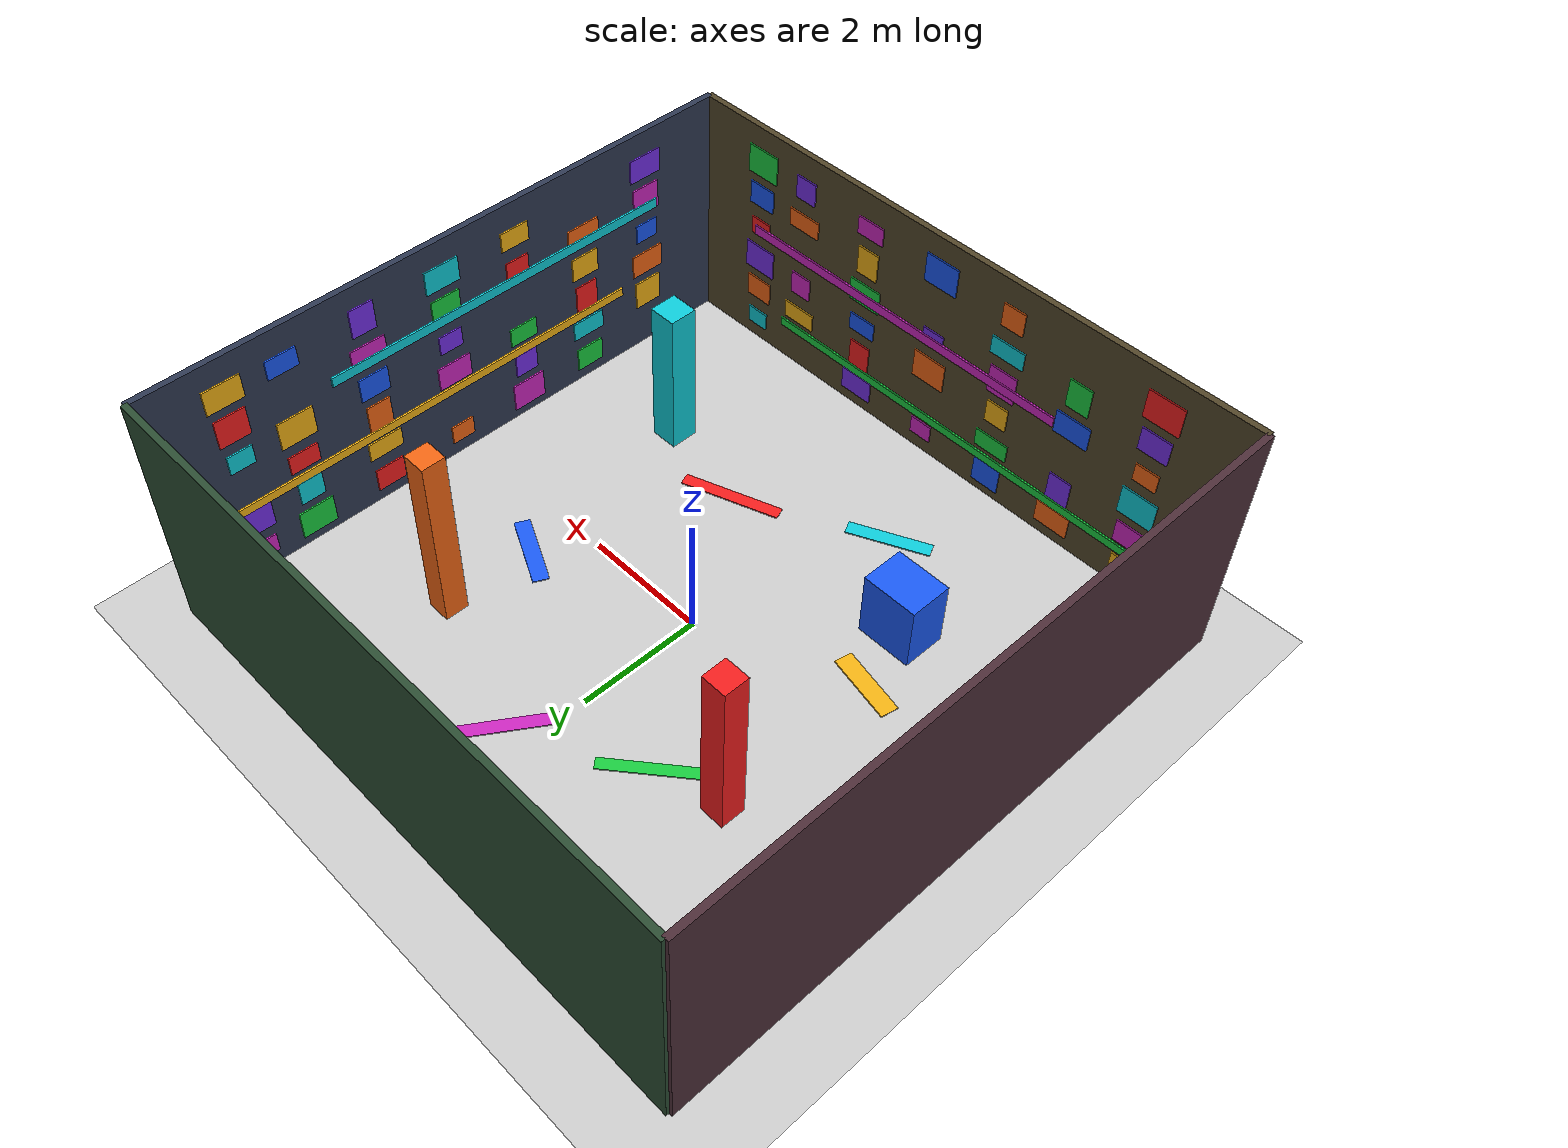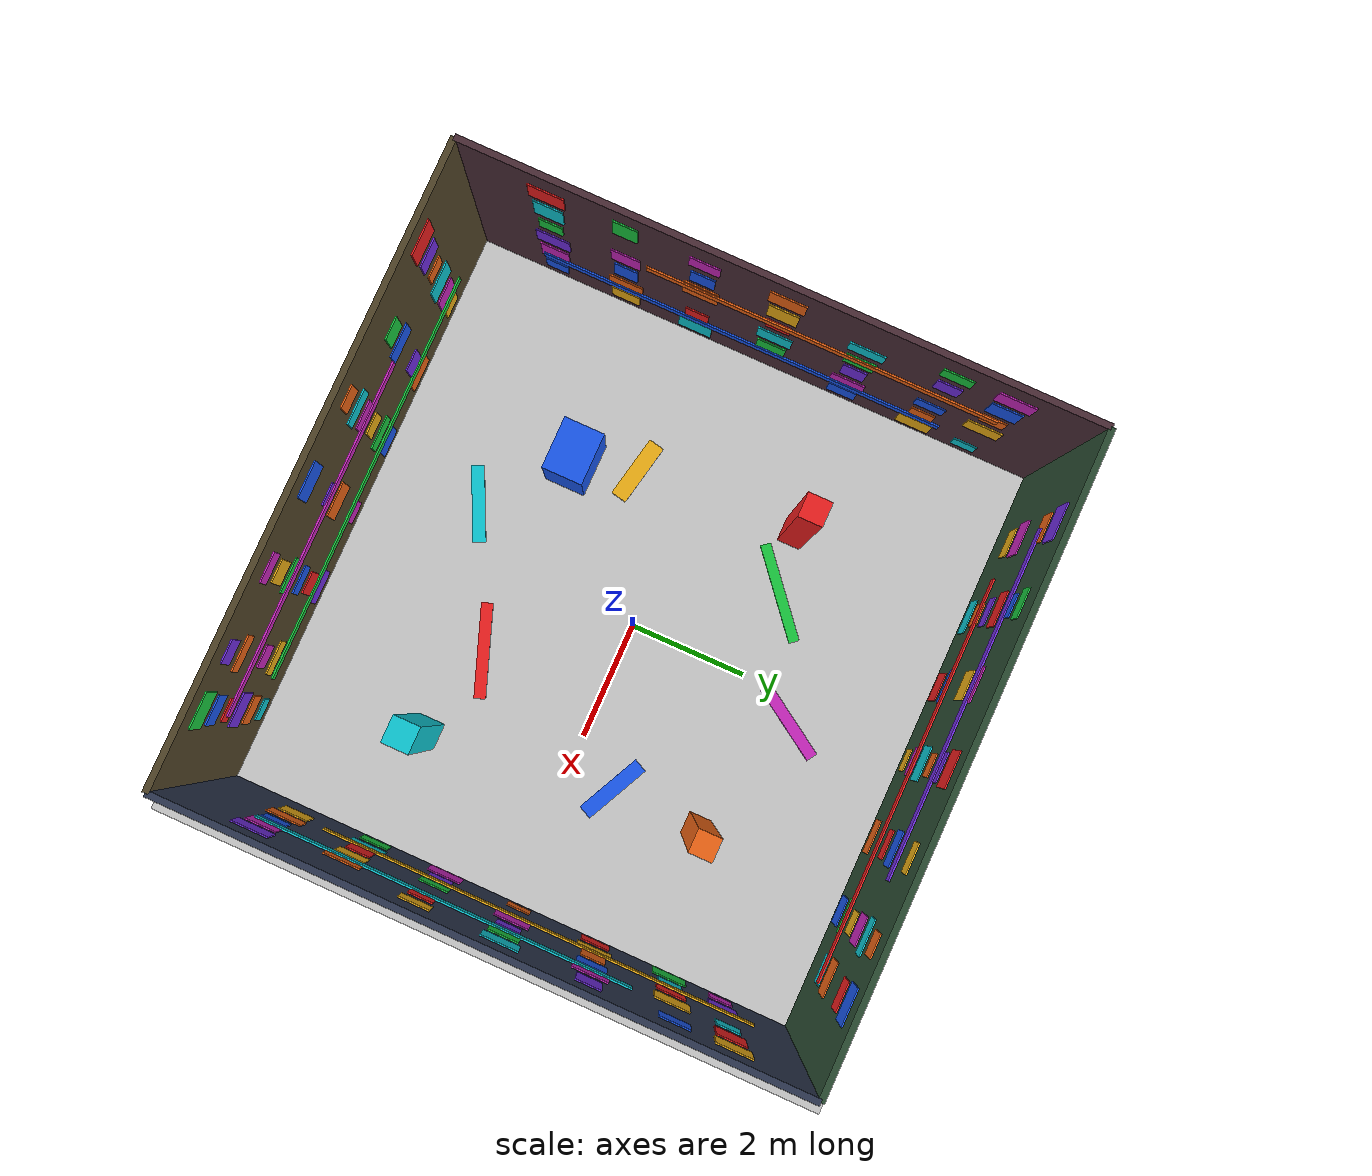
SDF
<sdf version="1.10">
 <world name="slam_room_office">
  <physics type="ode">
   <max_step_size>0.0040000000000000001</max_step_size>
   <real_time_factor>1</real_time_factor>
   <real_time_update_rate>250</real_time_update_rate>
  </physics>
  <gravity>0 0 -9.8000000000000007</gravity>
  <magnetic_field>6.0000000000000002e-06 2.3e-05 -4.1999999999999998e-05</magnetic_field>
  <atmosphere type="adiabatic"/>
  <scene>
   <grid>false</grid>
   <ambient>0.400000006 0.400000006 0.400000006 1</ambient>
   <background>0.699999988 0.699999988 0.699999988 1</background>
   <shadows>true</shadows>
  </scene>
  <spherical_coordinates>
   <surface_model>EARTH_WGS84</surface_model>
   <world_frame_orientation>ENU</world_frame_orientation>
   <latitude_deg>47.397971057728974</latitude_deg>
   <longitude_deg>8.5461637398001464</longitude_deg>
   <elevation>0</elevation>
   <heading_deg>0</heading_deg>
  </spherical_coordinates>
  <model name="ground_plane">
   <static>true</static>
   <link name="link">
    <collision name="collision">
     <geometry><plane><normal>0 0 1</normal><size>1 1</size></plane></geometry>
    </collision>
    <visual name="visual">
     <geometry><plane><normal>0 0 1</normal><size>500 500</size></plane></geometry>
     <material>
      <ambient>0.800000012 0.800000012 0.800000012 1</ambient>
      <diffuse>0.800000012 0.800000012 0.800000012 1</diffuse>
      <specular>0.800000012 0.800000012 0.800000012 1</specular>
     </material>
    </visual>
    <inertial>
     <mass>1</mass>
     <inertia><ixx>1</ixx><ixy>0</ixy><ixz>0</ixz><iyy>1</iyy><iyz>0</iyz><izz>1</izz></inertia>
    </inertial>
   </link>
  </model>
  <model name="slam_room_structure">
   <static>true</static>
   <link name="wall_x_pos">
    <pose>5 0 2 0 0 0</pose>
    <collision name="collision"><geometry><box><size>0.10000000000000001 10 4</size></box></geometry></collision>
    <visual name="visual">
     <geometry><box><size>0.10000000000000001 10 4</size></box></geometry>
     <material>
      <ambient>0.180000007 0.219999999 0.319999993 1</ambient>
      <diffuse>0.180000007 0.219999999 0.319999993 1</diffuse>
     </material>
    </visual>
    <inertial>
     <mass>1</mass>
     <inertia><ixx>1</ixx><ixy>0</ixy><ixz>0</ixz><iyy>1</iyy><iyz>0</iyz><izz>1</izz></inertia>
    </inertial>
   </link>
   <link name="wall_x_neg">
    <pose>-5 0 2 0 0 0</pose>
    <collision name="collision"><geometry><box><size>0.10000000000000001 10 4</size></box></geometry></collision>
    <visual name="visual">
     <geometry><box><size>0.10000000000000001 10 4</size></box></geometry>
     <material>
      <ambient>0.300000012 0.180000007 0.219999999 1</ambient>
      <diffuse>0.300000012 0.180000007 0.219999999 1</diffuse>
     </material>
    </visual>
    <inertial>
     <mass>1</mass>
     <inertia><ixx>1</ixx><ixy>0</ixy><ixz>0</ixz><iyy>1</iyy><iyz>0</iyz><izz>1</izz></inertia>
    </inertial>
   </link>
   <link name="wall_y_pos">
    <pose>0 5 2 0 0 0</pose>
    <collision name="collision"><geometry><box><size>10 0.10000000000000001 4</size></box></geometry></collision>
    <visual name="visual">
     <geometry><box><size>10 0.10000000000000001 4</size></box></geometry>
     <material>
      <ambient>0.170000002 0.300000012 0.200000003 1</ambient>
      <diffuse>0.170000002 0.300000012 0.200000003 1</diffuse>
     </material>
    </visual>
    <inertial>
     <mass>1</mass>
     <inertia><ixx>1</ixx><ixy>0</ixy><ixz>0</ixz><iyy>1</iyy><iyz>0</iyz><izz>1</izz></inertia>
    </inertial>
   </link>
   <link name="wall_y_neg">
    <pose>0 -5 2 0 0 0</pose>
    <collision name="collision"><geometry><box><size>10 0.10000000000000001 4</size></box></geometry></collision>
    <visual name="visual">
     <geometry><box><size>10 0.10000000000000001 4</size></box></geometry>
     <material>
      <ambient>0.319999993 0.270000011 0.159999996 1</ambient>
      <diffuse>0.319999993 0.270000011 0.159999996 1</diffuse>
     </material>
    </visual>
    <inertial>
     <mass>1</mass>
     <inertia><ixx>1</ixx><ixy>0</ixy><ixz>0</ixz><iyy>1</iyy><iyz>0</iyz><izz>1</izz></inertia>
    </inertial>
   </link>
   <link name="xwall_panel_0">
    <pose>4.9400000000000004 -2.3500000000000001 0.40000000000000002 0 0 0</pose>
    <visual name="visual">
     <geometry><box><size>0.025000000000000001 0.48999999999999999 0.40000000000000002</size></box></geometry>
     <material>
      <ambient>0.100000001 0.800000012 0.25 1</ambient>
      <diffuse>0.100000001 0.800000012 0.25 1</diffuse>
     </material>
    </visual>
    <inertial>
     <mass>1</mass>
     <inertia><ixx>1</ixx><ixy>0</ixy><ixz>0</ixz><iyy>1</iyy><iyz>0</iyz><izz>1</izz></inertia>
    </inertial>
   </link>
   <link name="xwall_panel_1">
    <pose>4.9400000000000004 -1.1000000000000001 0.40000000000000002 0 0 0</pose>
    <visual name="visual">
     <geometry><box><size>0.025000000000000001 0.57999999999999996 0.47999999999999998</size></box></geometry>
     <material>
      <ambient>0.800000012 0.150000006 0.75 1</ambient>
      <diffuse>0.800000012 0.150000006 0.75 1</diffuse>
     </material>
    </visual>
    <inertial>
     <mass>1</mass>
     <inertia><ixx>1</ixx><ixy>0</ixy><ixz>0</ixz><iyy>1</iyy><iyz>0</iyz><izz>1</izz></inertia>
    </inertial>
   </link>
   <link name="xwall_panel_2">
    <pose>4.9400000000000004 0.20000000000000001 0.40000000000000002 0 0 0</pose>
    <visual name="visual">
     <geometry><box><size>0.025000000000000001 0.40000000000000002 0.32000000000000001</size></box></geometry>
     <material>
      <ambient>0.949999988 0.400000006 0.0799999982 1</ambient>
      <diffuse>0.949999988 0.400000006 0.0799999982 1</diffuse>
     </material>
    </visual>
    <inertial>
     <mass>1</mass>
     <inertia><ixx>1</ixx><ixy>0</ixy><ixz>0</ixz><iyy>1</iyy><iyz>0</iyz><izz>1</izz></inertia>
    </inertial>
   </link>
   <link name="xwall_panel_3">
    <pose>4.9400000000000004 1.55 0.40000000000000002 0 0 0</pose>
    <visual name="visual">
     <geometry><box><size>0.025000000000000001 0.48999999999999999 0.40000000000000002</size></box></geometry>
     <material>
      <ambient>0.949999988 0.119999997 0.119999997 1</ambient>
      <diffuse>0.949999988 0.119999997 0.119999997 1</diffuse>
     </material>
    </visual>
    <inertial>
     <mass>1</mass>
     <inertia><ixx>1</ixx><ixy>0</ixy><ixz>0</ixz><iyy>1</iyy><iyz>0</iyz><izz>1</izz></inertia>
    </inertial>
   </link>
   <link name="xwall_panel_4">
    <pose>4.9400000000000004 2.8500000000000001 0.40000000000000002 0 0 0</pose>
    <visual name="visual">
     <geometry><box><size>0.025000000000000001 0.57999999999999996 0.47999999999999998</size></box></geometry>
     <material>
      <ambient>0.100000001 0.800000012 0.25 1</ambient>
      <diffuse>0.100000001 0.800000012 0.25 1</diffuse>
     </material>
    </visual>
    <inertial>
     <mass>1</mass>
     <inertia><ixx>1</ixx><ixy>0</ixy><ixz>0</ixz><iyy>1</iyy><iyz>0</iyz><izz>1</izz></inertia>
    </inertial>
   </link>
   <link name="xwall_panel_5">
    <pose>4.9400000000000004 3.75 0.40000000000000002 0 0 0</pose>
    <visual name="visual">
     <geometry><box><size>0.025000000000000001 0.40000000000000002 0.32000000000000001</size></box></geometry>
     <material>
      <ambient>0.800000012 0.150000006 0.75 1</ambient>
      <diffuse>0.800000012 0.150000006 0.75 1</diffuse>
     </material>
    </visual>
    <inertial>
     <mass>1</mass>
     <inertia><ixx>1</ixx><ixy>0</ixy><ixz>0</ixz><iyy>1</iyy><iyz>0</iyz><izz>1</izz></inertia>
    </inertial>
   </link>
   <link name="xwall_panel_6">
    <pose>4.9400000000000004 -3.6000000000000001 1 0 0 0</pose>
    <visual name="visual">
     <geometry><box><size>0.025000000000000001 0.48999999999999999 0.47999999999999998</size></box></geometry>
     <material>
      <ambient>0.949999988 0.699999988 0.0799999982 1</ambient>
      <diffuse>0.949999988 0.699999988 0.0799999982 1</diffuse>
     </material>
    </visual>
    <inertial>
     <mass>1</mass>
     <inertia><ixx>1</ixx><ixy>0</ixy><ixz>0</ixz><iyy>1</iyy><iyz>0</iyz><izz>1</izz></inertia>
    </inertial>
   </link>
   <link name="xwall_panel_7">
    <pose>4.9400000000000004 -2.3500000000000001 1 0 0 0</pose>
    <visual name="visual">
     <geometry><box><size>0.025000000000000001 0.57999999999999996 0.32000000000000001</size></box></geometry>
     <material>
      <ambient>0.0500000007 0.800000012 0.850000024 1</ambient>
      <diffuse>0.0500000007 0.800000012 0.850000024 1</diffuse>
     </material>
    </visual>
    <inertial>
     <mass>1</mass>
     <inertia><ixx>1</ixx><ixy>0</ixy><ixz>0</ixz><iyy>1</iyy><iyz>0</iyz><izz>1</izz></inertia>
    </inertial>
   </link>
   <link name="xwall_panel_8">
    <pose>4.9400000000000004 -1.1000000000000001 1 0 0 0</pose>
    <visual name="visual">
     <geometry><box><size>0.025000000000000001 0.40000000000000002 0.40000000000000002</size></box></geometry>
     <material>
      <ambient>0.449999988 0.180000007 0.899999976 1</ambient>
      <diffuse>0.449999988 0.180000007 0.899999976 1</diffuse>
     </material>
    </visual>
    <inertial>
     <mass>1</mass>
     <inertia><ixx>1</ixx><ixy>0</ixy><ixz>0</ixz><iyy>1</iyy><iyz>0</iyz><izz>1</izz></inertia>
    </inertial>
   </link>
   <link name="xwall_panel_9">
    <pose>4.9400000000000004 1.55 1 0 0 0</pose>
    <visual name="visual">
     <geometry><box><size>0.025000000000000001 0.57999999999999996 0.32000000000000001</size></box></geometry>
     <material>
      <ambient>0.949999988 0.699999988 0.0799999982 1</ambient>
      <diffuse>0.949999988 0.699999988 0.0799999982 1</diffuse>
     </material>
    </visual>
    <inertial>
     <mass>1</mass>
     <inertia><ixx>1</ixx><ixy>0</ixy><ixz>0</ixz><iyy>1</iyy><iyz>0</iyz><izz>1</izz></inertia>
    </inertial>
   </link>
   <link name="xwall_panel_10">
    <pose>4.9400000000000004 2.8500000000000001 1 0 0 0</pose>
    <visual name="visual">
     <geometry><box><size>0.025000000000000001 0.40000000000000002 0.40000000000000002</size></box></geometry>
     <material>
      <ambient>0.0500000007 0.800000012 0.850000024 1</ambient>
      <diffuse>0.0500000007 0.800000012 0.850000024 1</diffuse>
     </material>
    </visual>
    <inertial>
     <mass>1</mass>
     <inertia><ixx>1</ixx><ixy>0</ixy><ixz>0</ixz><iyy>1</iyy><iyz>0</iyz><izz>1</izz></inertia>
    </inertial>
   </link>
   <link name="xwall_panel_11">
    <pose>4.9400000000000004 3.75 1 0 0 0</pose>
    <visual name="visual">
     <geometry><box><size>0.025000000000000001 0.48999999999999999 0.47999999999999998</size></box></geometry>
     <material>
      <ambient>0.449999988 0.180000007 0.899999976 1</ambient>
      <diffuse>0.449999988 0.180000007 0.899999976 1</diffuse>
     </material>
    </visual>
    <inertial>
     <mass>1</mass>
     <inertia><ixx>1</ixx><ixy>0</ixy><ixz>0</ixz><iyy>1</iyy><iyz>0</iyz><izz>1</izz></inertia>
    </inertial>
   </link>
   <link name="xwall_panel_12">
    <pose>4.9400000000000004 -3.6000000000000001 1.6000000000000001 0 0 0</pose>
    <visual name="visual">
     <geometry><box><size>0.025000000000000001 0.57999999999999996 0.40000000000000002</size></box></geometry>
     <material>
      <ambient>0.949999988 0.400000006 0.0799999982 1</ambient>
      <diffuse>0.949999988 0.400000006 0.0799999982 1</diffuse>
     </material>
    </visual>
    <inertial>
     <mass>1</mass>
     <inertia><ixx>1</ixx><ixy>0</ixy><ixz>0</ixz><iyy>1</iyy><iyz>0</iyz><izz>1</izz></inertia>
    </inertial>
   </link>
   <link name="xwall_panel_13">
    <pose>4.9400000000000004 -2.3500000000000001 1.6000000000000001 0 0 0</pose>
    <visual name="visual">
     <geometry><box><size>0.025000000000000001 0.40000000000000002 0.47999999999999998</size></box></geometry>
     <material>
      <ambient>0.949999988 0.119999997 0.119999997 1</ambient>
      <diffuse>0.949999988 0.119999997 0.119999997 1</diffuse>
     </material>
    </visual>
    <inertial>
     <mass>1</mass>
     <inertia><ixx>1</ixx><ixy>0</ixy><ixz>0</ixz><iyy>1</iyy><iyz>0</iyz><izz>1</izz></inertia>
    </inertial>
   </link>
   <link name="xwall_panel_14">
    <pose>4.9400000000000004 -1.1000000000000001 1.6000000000000001 0 0 0</pose>
    <visual name="visual">
     <geometry><box><size>0.025000000000000001 0.48999999999999999 0.32000000000000001</size></box></geometry>
     <material>
      <ambient>0.100000001 0.800000012 0.25 1</ambient>
      <diffuse>0.100000001 0.800000012 0.25 1</diffuse>
     </material>
    </visual>
    <inertial>
     <mass>1</mass>
     <inertia><ixx>1</ixx><ixy>0</ixy><ixz>0</ixz><iyy>1</iyy><iyz>0</iyz><izz>1</izz></inertia>
    </inertial>
   </link>
   <link name="xwall_panel_15">
    <pose>4.9400000000000004 0.20000000000000001 1.6000000000000001 0 0 0</pose>
    <visual name="visual">
     <geometry><box><size>0.025000000000000001 0.57999999999999996 0.40000000000000002</size></box></geometry>
     <material>
      <ambient>0.800000012 0.150000006 0.75 1</ambient>
      <diffuse>0.800000012 0.150000006 0.75 1</diffuse>
     </material>
    </visual>
    <inertial>
     <mass>1</mass>
     <inertia><ixx>1</ixx><ixy>0</ixy><ixz>0</ixz><iyy>1</iyy><iyz>0</iyz><izz>1</izz></inertia>
    </inertial>
   </link>
   <link name="xwall_panel_16">
    <pose>4.9400000000000004 1.55 1.6000000000000001 0 0 0</pose>
    <visual name="visual">
     <geometry><box><size>0.025000000000000001 0.40000000000000002 0.47999999999999998</size></box></geometry>
     <material>
      <ambient>0.949999988 0.400000006 0.0799999982 1</ambient>
      <diffuse>0.949999988 0.400000006 0.0799999982 1</diffuse>
     </material>
    </visual>
    <inertial>
     <mass>1</mass>
     <inertia><ixx>1</ixx><ixy>0</ixy><ixz>0</ixz><iyy>1</iyy><iyz>0</iyz><izz>1</izz></inertia>
    </inertial>
   </link>
   <link name="xwall_panel_17">
    <pose>4.9400000000000004 2.8500000000000001 1.6000000000000001 0 0 0</pose>
    <visual name="visual">
     <geometry><box><size>0.025000000000000001 0.48999999999999999 0.32000000000000001</size></box></geometry>
     <material>
      <ambient>0.949999988 0.119999997 0.119999997 1</ambient>
      <diffuse>0.949999988 0.119999997 0.119999997 1</diffuse>
     </material>
    </visual>
    <inertial>
     <mass>1</mass>
     <inertia><ixx>1</ixx><ixy>0</ixy><ixz>0</ixz><iyy>1</iyy><iyz>0</iyz><izz>1</izz></inertia>
    </inertial>
   </link>
   <link name="xwall_panel_18">
    <pose>4.9400000000000004 -3.6000000000000001 2.2000000000000002 0 0 0</pose>
    <visual name="visual">
     <geometry><box><size>0.025000000000000001 0.40000000000000002 0.32000000000000001</size></box></geometry>
     <material>
      <ambient>0.100000001 0.349999994 0.949999988 1</ambient>
      <diffuse>0.100000001 0.349999994 0.949999988 1</diffuse>
     </material>
    </visual>
    <inertial>
     <mass>1</mass>
     <inertia><ixx>1</ixx><ixy>0</ixy><ixz>0</ixz><iyy>1</iyy><iyz>0</iyz><izz>1</izz></inertia>
    </inertial>
   </link>
   <link name="xwall_panel_19">
    <pose>4.9400000000000004 -2.3500000000000001 2.2000000000000002 0 0 0</pose>
    <visual name="visual">
     <geometry><box><size>0.025000000000000001 0.48999999999999999 0.40000000000000002</size></box></geometry>
     <material>
      <ambient>0.949999988 0.699999988 0.0799999982 1</ambient>
      <diffuse>0.949999988 0.699999988 0.0799999982 1</diffuse>
     </material>
    </visual>
    <inertial>
     <mass>1</mass>
     <inertia><ixx>1</ixx><ixy>0</ixy><ixz>0</ixz><iyy>1</iyy><iyz>0</iyz><izz>1</izz></inertia>
    </inertial>
   </link>
   <link name="xwall_panel_20">
    <pose>4.9400000000000004 0.20000000000000001 2.2000000000000002 0 0 0</pose>
    <visual name="visual">
     <geometry><box><size>0.025000000000000001 0.40000000000000002 0.32000000000000001</size></box></geometry>
     <material>
      <ambient>0.449999988 0.180000007 0.899999976 1</ambient>
      <diffuse>0.449999988 0.180000007 0.899999976 1</diffuse>
     </material>
    </visual>
    <inertial>
     <mass>1</mass>
     <inertia><ixx>1</ixx><ixy>0</ixy><ixz>0</ixz><iyy>1</iyy><iyz>0</iyz><izz>1</izz></inertia>
    </inertial>
   </link>
   <link name="xwall_panel_21">
    <pose>4.9400000000000004 1.55 2.2000000000000002 0 0 0</pose>
    <visual name="visual">
     <geometry><box><size>0.025000000000000001 0.48999999999999999 0.40000000000000002</size></box></geometry>
     <material>
      <ambient>0.100000001 0.349999994 0.949999988 1</ambient>
      <diffuse>0.100000001 0.349999994 0.949999988 1</diffuse>
     </material>
    </visual>
    <inertial>
     <mass>1</mass>
     <inertia><ixx>1</ixx><ixy>0</ixy><ixz>0</ixz><iyy>1</iyy><iyz>0</iyz><izz>1</izz></inertia>
    </inertial>
   </link>
   <link name="xwall_panel_22">
    <pose>4.9400000000000004 2.8500000000000001 2.2000000000000002 0 0 0</pose>
    <visual name="visual">
     <geometry><box><size>0.025000000000000001 0.57999999999999996 0.47999999999999998</size></box></geometry>
     <material>
      <ambient>0.949999988 0.699999988 0.0799999982 1</ambient>
      <diffuse>0.949999988 0.699999988 0.0799999982 1</diffuse>
     </material>
    </visual>
    <inertial>
     <mass>1</mass>
     <inertia><ixx>1</ixx><ixy>0</ixy><ixz>0</ixz><iyy>1</iyy><iyz>0</iyz><izz>1</izz></inertia>
    </inertial>
   </link>
   <link name="xwall_panel_23">
    <pose>4.9400000000000004 3.75 2.2000000000000002 0 0 0</pose>
    <visual name="visual">
     <geometry><box><size>0.025000000000000001 0.40000000000000002 0.32000000000000001</size></box></geometry>
     <material>
      <ambient>0.0500000007 0.800000012 0.850000024 1</ambient>
      <diffuse>0.0500000007 0.800000012 0.850000024 1</diffuse>
     </material>
    </visual>
    <inertial>
     <mass>1</mass>
     <inertia><ixx>1</ixx><ixy>0</ixy><ixz>0</ixz><iyy>1</iyy><iyz>0</iyz><izz>1</izz></inertia>
    </inertial>
   </link>
   <link name="xwall_panel_24">
    <pose>4.9400000000000004 -3.6000000000000001 2.7999999999999998 0 0 0</pose>
    <visual name="visual">
     <geometry><box><size>0.025000000000000001 0.48999999999999999 0.47999999999999998</size></box></geometry>
     <material>
      <ambient>0.800000012 0.150000006 0.75 1</ambient>
      <diffuse>0.800000012 0.150000006 0.75 1</diffuse>
     </material>
    </visual>
    <inertial>
     <mass>1</mass>
     <inertia><ixx>1</ixx><ixy>0</ixy><ixz>0</ixz><iyy>1</iyy><iyz>0</iyz><izz>1</izz></inertia>
    </inertial>
   </link>
   <link name="xwall_panel_25">
    <pose>4.9400000000000004 -2.3500000000000001 2.7999999999999998 0 0 0</pose>
    <visual name="visual">
     <geometry><box><size>0.025000000000000001 0.57999999999999996 0.32000000000000001</size></box></geometry>
     <material>
      <ambient>0.949999988 0.400000006 0.0799999982 1</ambient>
      <diffuse>0.949999988 0.400000006 0.0799999982 1</diffuse>
     </material>
    </visual>
    <inertial>
     <mass>1</mass>
     <inertia><ixx>1</ixx><ixy>0</ixy><ixz>0</ixz><iyy>1</iyy><iyz>0</iyz><izz>1</izz></inertia>
    </inertial>
   </link>
   <link name="xwall_panel_26">
    <pose>4.9400000000000004 -1.1000000000000001 2.7999999999999998 0 0 0</pose>
    <visual name="visual">
     <geometry><box><size>0.025000000000000001 0.40000000000000002 0.40000000000000002</size></box></geometry>
     <material>
      <ambient>0.949999988 0.119999997 0.119999997 1</ambient>
      <diffuse>0.949999988 0.119999997 0.119999997 1</diffuse>
     </material>
    </visual>
    <inertial>
     <mass>1</mass>
     <inertia><ixx>1</ixx><ixy>0</ixy><ixz>0</ixz><iyy>1</iyy><iyz>0</iyz><izz>1</izz></inertia>
    </inertial>
   </link>
   <link name="xwall_panel_27">
    <pose>4.9400000000000004 0.20000000000000001 2.7999999999999998 0 0 0</pose>
    <visual name="visual">
     <geometry><box><size>0.025000000000000001 0.48999999999999999 0.47999999999999998</size></box></geometry>
     <material>
      <ambient>0.100000001 0.800000012 0.25 1</ambient>
      <diffuse>0.100000001 0.800000012 0.25 1</diffuse>
     </material>
    </visual>
    <inertial>
     <mass>1</mass>
     <inertia><ixx>1</ixx><ixy>0</ixy><ixz>0</ixz><iyy>1</iyy><iyz>0</iyz><izz>1</izz></inertia>
    </inertial>
   </link>
   <link name="xwall_panel_28">
    <pose>4.9400000000000004 1.55 2.7999999999999998 0 0 0</pose>
    <visual name="visual">
     <geometry><box><size>0.025000000000000001 0.57999999999999996 0.32000000000000001</size></box></geometry>
     <material>
      <ambient>0.800000012 0.150000006 0.75 1</ambient>
      <diffuse>0.800000012 0.150000006 0.75 1</diffuse>
     </material>
    </visual>
    <inertial>
     <mass>1</mass>
     <inertia><ixx>1</ixx><ixy>0</ixy><ixz>0</ixz><iyy>1</iyy><iyz>0</iyz><izz>1</izz></inertia>
    </inertial>
   </link>
   <link name="xwall_panel_29">
    <pose>4.9400000000000004 3.75 2.7999999999999998 0 0 0</pose>
    <visual name="visual">
     <geometry><box><size>0.025000000000000001 0.48999999999999999 0.47999999999999998</size></box></geometry>
     <material>
      <ambient>0.949999988 0.119999997 0.119999997 1</ambient>
      <diffuse>0.949999988 0.119999997 0.119999997 1</diffuse>
     </material>
    </visual>
    <inertial>
     <mass>1</mass>
     <inertia><ixx>1</ixx><ixy>0</ixy><ixz>0</ixz><iyy>1</iyy><iyz>0</iyz><izz>1</izz></inertia>
    </inertial>
   </link>
   <link name="xwall_panel_30">
    <pose>4.9400000000000004 -3.6000000000000001 3.3999999999999999 0 0 0</pose>
    <visual name="visual">
     <geometry><box><size>0.025000000000000001 0.57999999999999996 0.40000000000000002</size></box></geometry>
     <material>
      <ambient>0.449999988 0.180000007 0.899999976 1</ambient>
      <diffuse>0.449999988 0.180000007 0.899999976 1</diffuse>
     </material>
    </visual>
    <inertial>
     <mass>1</mass>
     <inertia><ixx>1</ixx><ixy>0</ixy><ixz>0</ixz><iyy>1</iyy><iyz>0</iyz><izz>1</izz></inertia>
    </inertial>
   </link>
   <link name="xwall_panel_31">
    <pose>4.9400000000000004 -1.1000000000000001 3.3999999999999999 0 0 0</pose>
    <visual name="visual">
     <geometry><box><size>0.025000000000000001 0.48999999999999999 0.32000000000000001</size></box></geometry>
     <material>
      <ambient>0.949999988 0.699999988 0.0799999982 1</ambient>
      <diffuse>0.949999988 0.699999988 0.0799999982 1</diffuse>
     </material>
    </visual>
    <inertial>
     <mass>1</mass>
     <inertia><ixx>1</ixx><ixy>0</ixy><ixz>0</ixz><iyy>1</iyy><iyz>0</iyz><izz>1</izz></inertia>
    </inertial>
   </link>
   <link name="xwall_panel_32">
    <pose>4.9400000000000004 0.20000000000000001 3.3999999999999999 0 0 0</pose>
    <visual name="visual">
     <geometry><box><size>0.025000000000000001 0.57999999999999996 0.40000000000000002</size></box></geometry>
     <material>
      <ambient>0.0500000007 0.800000012 0.850000024 1</ambient>
      <diffuse>0.0500000007 0.800000012 0.850000024 1</diffuse>
     </material>
    </visual>
    <inertial>
     <mass>1</mass>
     <inertia><ixx>1</ixx><ixy>0</ixy><ixz>0</ixz><iyy>1</iyy><iyz>0</iyz><izz>1</izz></inertia>
    </inertial>
   </link>
   <link name="xwall_panel_33">
    <pose>4.9400000000000004 1.55 3.3999999999999999 0 0 0</pose>
    <visual name="visual">
     <geometry><box><size>0.025000000000000001 0.40000000000000002 0.47999999999999998</size></box></geometry>
     <material>
      <ambient>0.449999988 0.180000007 0.899999976 1</ambient>
      <diffuse>0.449999988 0.180000007 0.899999976 1</diffuse>
     </material>
    </visual>
    <inertial>
     <mass>1</mass>
     <inertia><ixx>1</ixx><ixy>0</ixy><ixz>0</ixz><iyy>1</iyy><iyz>0</iyz><izz>1</izz></inertia>
    </inertial>
   </link>
   <link name="xwall_panel_34">
    <pose>4.9400000000000004 2.8500000000000001 3.3999999999999999 0 0 0</pose>
    <visual name="visual">
     <geometry><box><size>0.025000000000000001 0.48999999999999999 0.32000000000000001</size></box></geometry>
     <material>
      <ambient>0.100000001 0.349999994 0.949999988 1</ambient>
      <diffuse>0.100000001 0.349999994 0.949999988 1</diffuse>
     </material>
    </visual>
    <inertial>
     <mass>1</mass>
     <inertia><ixx>1</ixx><ixy>0</ixy><ixz>0</ixz><iyy>1</iyy><iyz>0</iyz><izz>1</izz></inertia>
    </inertial>
   </link>
   <link name="xwall_panel_35">
    <pose>4.9400000000000004 3.75 3.3999999999999999 0 0 0</pose>
    <visual name="visual">
     <geometry><box><size>0.025000000000000001 0.57999999999999996 0.40000000000000002</size></box></geometry>
     <material>
      <ambient>0.949999988 0.699999988 0.0799999982 1</ambient>
      <diffuse>0.949999988 0.699999988 0.0799999982 1</diffuse>
     </material>
    </visual>
    <inertial>
     <mass>1</mass>
     <inertia><ixx>1</ixx><ixy>0</ixy><ixz>0</ixz><iyy>1</iyy><iyz>0</iyz><izz>1</izz></inertia>
    </inertial>
   </link>
   <link name="xwall_panel_36">
    <pose>-4.9400000000000004 -3.6000000000000001 0.40000000000000002 0 0 0</pose>
    <visual name="visual">
     <geometry><box><size>0.025000000000000001 0.40000000000000002 0.32000000000000001</size></box></geometry>
     <material>
      <ambient>0.100000001 0.349999994 0.949999988 1</ambient>
      <diffuse>0.100000001 0.349999994 0.949999988 1</diffuse>
     </material>
    </visual>
    <inertial>
     <mass>1</mass>
     <inertia><ixx>1</ixx><ixy>0</ixy><ixz>0</ixz><iyy>1</iyy><iyz>0</iyz><izz>1</izz></inertia>
    </inertial>
   </link>
   <link name="xwall_panel_37">
    <pose>-4.9400000000000004 -2.3500000000000001 0.40000000000000002 0 0 0</pose>
    <visual name="visual">
     <geometry><box><size>0.025000000000000001 0.48999999999999999 0.40000000000000002</size></box></geometry>
     <material>
      <ambient>0.949999988 0.699999988 0.0799999982 1</ambient>
      <diffuse>0.949999988 0.699999988 0.0799999982 1</diffuse>
     </material>
    </visual>
    <inertial>
     <mass>1</mass>
     <inertia><ixx>1</ixx><ixy>0</ixy><ixz>0</ixz><iyy>1</iyy><iyz>0</iyz><izz>1</izz></inertia>
    </inertial>
   </link>
   <link name="xwall_panel_38">
    <pose>-4.9400000000000004 -1.1000000000000001 0.40000000000000002 0 0 0</pose>
    <visual name="visual">
     <geometry><box><size>0.025000000000000001 0.57999999999999996 0.47999999999999998</size></box></geometry>
     <material>
      <ambient>0.0500000007 0.800000012 0.850000024 1</ambient>
      <diffuse>0.0500000007 0.800000012 0.850000024 1</diffuse>
     </material>
    </visual>
    <inertial>
     <mass>1</mass>
     <inertia><ixx>1</ixx><ixy>0</ixy><ixz>0</ixz><iyy>1</iyy><iyz>0</iyz><izz>1</izz></inertia>
    </inertial>
   </link>
   <link name="xwall_panel_39">
    <pose>-4.9400000000000004 1.55 0.40000000000000002 0 0 0</pose>
    <visual name="visual">
     <geometry><box><size>0.025000000000000001 0.48999999999999999 0.40000000000000002</size></box></geometry>
     <material>
      <ambient>0.100000001 0.349999994 0.949999988 1</ambient>
      <diffuse>0.100000001 0.349999994 0.949999988 1</diffuse>
     </material>
    </visual>
    <inertial>
     <mass>1</mass>
     <inertia><ixx>1</ixx><ixy>0</ixy><ixz>0</ixz><iyy>1</iyy><iyz>0</iyz><izz>1</izz></inertia>
    </inertial>
   </link>
   <link name="xwall_panel_40">
    <pose>-4.9400000000000004 2.8500000000000001 0.40000000000000002 0 0 0</pose>
    <visual name="visual">
     <geometry><box><size>0.025000000000000001 0.57999999999999996 0.47999999999999998</size></box></geometry>
     <material>
      <ambient>0.949999988 0.699999988 0.0799999982 1</ambient>
      <diffuse>0.949999988 0.699999988 0.0799999982 1</diffuse>
     </material>
    </visual>
    <inertial>
     <mass>1</mass>
     <inertia><ixx>1</ixx><ixy>0</ixy><ixz>0</ixz><iyy>1</iyy><iyz>0</iyz><izz>1</izz></inertia>
    </inertial>
   </link>
   <link name="xwall_panel_41">
    <pose>-4.9400000000000004 3.75 0.40000000000000002 0 0 0</pose>
    <visual name="visual">
     <geometry><box><size>0.025000000000000001 0.40000000000000002 0.32000000000000001</size></box></geometry>
     <material>
      <ambient>0.0500000007 0.800000012 0.850000024 1</ambient>
      <diffuse>0.0500000007 0.800000012 0.850000024 1</diffuse>
     </material>
    </visual>
    <inertial>
     <mass>1</mass>
     <inertia><ixx>1</ixx><ixy>0</ixy><ixz>0</ixz><iyy>1</iyy><iyz>0</iyz><izz>1</izz></inertia>
    </inertial>
   </link>
   <link name="xwall_panel_42">
    <pose>-4.9400000000000004 -3.6000000000000001 1 0 0 0</pose>
    <visual name="visual">
     <geometry><box><size>0.025000000000000001 0.48999999999999999 0.47999999999999998</size></box></geometry>
     <material>
      <ambient>0.800000012 0.150000006 0.75 1</ambient>
      <diffuse>0.800000012 0.150000006 0.75 1</diffuse>
     </material>
    </visual>
    <inertial>
     <mass>1</mass>
     <inertia><ixx>1</ixx><ixy>0</ixy><ixz>0</ixz><iyy>1</iyy><iyz>0</iyz><izz>1</izz></inertia>
    </inertial>
   </link>
   <link name="xwall_panel_43">
    <pose>-4.9400000000000004 -2.3500000000000001 1 0 0 0</pose>
    <visual name="visual">
     <geometry><box><size>0.025000000000000001 0.57999999999999996 0.32000000000000001</size></box></geometry>
     <material>
      <ambient>0.949999988 0.400000006 0.0799999982 1</ambient>
      <diffuse>0.949999988 0.400000006 0.0799999982 1</diffuse>
     </material>
    </visual>
    <inertial>
     <mass>1</mass>
     <inertia><ixx>1</ixx><ixy>0</ixy><ixz>0</ixz><iyy>1</iyy><iyz>0</iyz><izz>1</izz></inertia>
    </inertial>
   </link>
   <link name="xwall_panel_44">
    <pose>-4.9400000000000004 -1.1000000000000001 1 0 0 0</pose>
    <visual name="visual">
     <geometry><box><size>0.025000000000000001 0.40000000000000002 0.40000000000000002</size></box></geometry>
     <material>
      <ambient>0.949999988 0.119999997 0.119999997 1</ambient>
      <diffuse>0.949999988 0.119999997 0.119999997 1</diffuse>
     </material>
    </visual>
    <inertial>
     <mass>1</mass>
     <inertia><ixx>1</ixx><ixy>0</ixy><ixz>0</ixz><iyy>1</iyy><iyz>0</iyz><izz>1</izz></inertia>
    </inertial>
   </link>
   <link name="xwall_panel_45">
    <pose>-4.9400000000000004 0.20000000000000001 1 0 0 0</pose>
    <visual name="visual">
     <geometry><box><size>0.025000000000000001 0.48999999999999999 0.47999999999999998</size></box></geometry>
     <material>
      <ambient>0.100000001 0.800000012 0.25 1</ambient>
      <diffuse>0.100000001 0.800000012 0.25 1</diffuse>
     </material>
    </visual>
    <inertial>
     <mass>1</mass>
     <inertia><ixx>1</ixx><ixy>0</ixy><ixz>0</ixz><iyy>1</iyy><iyz>0</iyz><izz>1</izz></inertia>
    </inertial>
   </link>
   <link name="xwall_panel_46">
    <pose>-4.9400000000000004 1.55 1 0 0 0</pose>
    <visual name="visual">
     <geometry><box><size>0.025000000000000001 0.57999999999999996 0.32000000000000001</size></box></geometry>
     <material>
      <ambient>0.800000012 0.150000006 0.75 1</ambient>
      <diffuse>0.800000012 0.150000006 0.75 1</diffuse>
     </material>
    </visual>
    <inertial>
     <mass>1</mass>
     <inertia><ixx>1</ixx><ixy>0</ixy><ixz>0</ixz><iyy>1</iyy><iyz>0</iyz><izz>1</izz></inertia>
    </inertial>
   </link>
   <link name="xwall_panel_47">
    <pose>-4.9400000000000004 2.8500000000000001 1 0 0 0</pose>
    <visual name="visual">
     <geometry><box><size>0.025000000000000001 0.40000000000000002 0.40000000000000002</size></box></geometry>
     <material>
      <ambient>0.949999988 0.400000006 0.0799999982 1</ambient>
      <diffuse>0.949999988 0.400000006 0.0799999982 1</diffuse>
     </material>
    </visual>
    <inertial>
     <mass>1</mass>
     <inertia><ixx>1</ixx><ixy>0</ixy><ixz>0</ixz><iyy>1</iyy><iyz>0</iyz><izz>1</izz></inertia>
    </inertial>
   </link>
   <link name="xwall_panel_48">
    <pose>-4.9400000000000004 -3.6000000000000001 1.6000000000000001 0 0 0</pose>
    <visual name="visual">
     <geometry><box><size>0.025000000000000001 0.57999999999999996 0.40000000000000002</size></box></geometry>
     <material>
      <ambient>0.449999988 0.180000007 0.899999976 1</ambient>
      <diffuse>0.449999988 0.180000007 0.899999976 1</diffuse>
     </material>
    </visual>
    <inertial>
     <mass>1</mass>
     <inertia><ixx>1</ixx><ixy>0</ixy><ixz>0</ixz><iyy>1</iyy><iyz>0</iyz><izz>1</izz></inertia>
    </inertial>
   </link>
   <link name="xwall_panel_49">
    <pose>-4.9400000000000004 -2.3500000000000001 1.6000000000000001 0 0 0</pose>
    <visual name="visual">
     <geometry><box><size>0.025000000000000001 0.40000000000000002 0.47999999999999998</size></box></geometry>
     <material>
      <ambient>0.100000001 0.349999994 0.949999988 1</ambient>
      <diffuse>0.100000001 0.349999994 0.949999988 1</diffuse>
     </material>
    </visual>
    <inertial>
     <mass>1</mass>
     <inertia><ixx>1</ixx><ixy>0</ixy><ixz>0</ixz><iyy>1</iyy><iyz>0</iyz><izz>1</izz></inertia>
    </inertial>
   </link>
   <link name="xwall_panel_50">
    <pose>-4.9400000000000004 0.20000000000000001 1.6000000000000001 0 0 0</pose>
    <visual name="visual">
     <geometry><box><size>0.025000000000000001 0.57999999999999996 0.40000000000000002</size></box></geometry>
     <material>
      <ambient>0.0500000007 0.800000012 0.850000024 1</ambient>
      <diffuse>0.0500000007 0.800000012 0.850000024 1</diffuse>
     </material>
    </visual>
    <inertial>
     <mass>1</mass>
     <inertia><ixx>1</ixx><ixy>0</ixy><ixz>0</ixz><iyy>1</iyy><iyz>0</iyz><izz>1</izz></inertia>
    </inertial>
   </link>
   <link name="xwall_panel_51">
    <pose>-4.9400000000000004 1.55 1.6000000000000001 0 0 0</pose>
    <visual name="visual">
     <geometry><box><size>0.025000000000000001 0.40000000000000002 0.47999999999999998</size></box></geometry>
     <material>
      <ambient>0.449999988 0.180000007 0.899999976 1</ambient>
      <diffuse>0.449999988 0.180000007 0.899999976 1</diffuse>
     </material>
    </visual>
    <inertial>
     <mass>1</mass>
     <inertia><ixx>1</ixx><ixy>0</ixy><ixz>0</ixz><iyy>1</iyy><iyz>0</iyz><izz>1</izz></inertia>
    </inertial>
   </link>
   <link name="xwall_panel_52">
    <pose>-4.9400000000000004 2.8500000000000001 1.6000000000000001 0 0 0</pose>
    <visual name="visual">
     <geometry><box><size>0.025000000000000001 0.48999999999999999 0.32000000000000001</size></box></geometry>
     <material>
      <ambient>0.100000001 0.349999994 0.949999988 1</ambient>
      <diffuse>0.100000001 0.349999994 0.949999988 1</diffuse>
     </material>
    </visual>
    <inertial>
     <mass>1</mass>
     <inertia><ixx>1</ixx><ixy>0</ixy><ixz>0</ixz><iyy>1</iyy><iyz>0</iyz><izz>1</izz></inertia>
    </inertial>
   </link>
   <link name="xwall_panel_53">
    <pose>-4.9400000000000004 3.75 1.6000000000000001 0 0 0</pose>
    <visual name="visual">
     <geometry><box><size>0.025000000000000001 0.57999999999999996 0.40000000000000002</size></box></geometry>
     <material>
      <ambient>0.949999988 0.699999988 0.0799999982 1</ambient>
      <diffuse>0.949999988 0.699999988 0.0799999982 1</diffuse>
     </material>
    </visual>
    <inertial>
     <mass>1</mass>
     <inertia><ixx>1</ixx><ixy>0</ixy><ixz>0</ixz><iyy>1</iyy><iyz>0</iyz><izz>1</izz></inertia>
    </inertial>
   </link>
   <link name="xwall_panel_54">
    <pose>-4.9400000000000004 -3.6000000000000001 2.2000000000000002 0 0 0</pose>
    <visual name="visual">
     <geometry><box><size>0.025000000000000001 0.40000000000000002 0.32000000000000001</size></box></geometry>
     <material>
      <ambient>0.100000001 0.800000012 0.25 1</ambient>
      <diffuse>0.100000001 0.800000012 0.25 1</diffuse>
     </material>
    </visual>
    <inertial>
     <mass>1</mass>
     <inertia><ixx>1</ixx><ixy>0</ixy><ixz>0</ixz><iyy>1</iyy><iyz>0</iyz><izz>1</izz></inertia>
    </inertial>
   </link>
   <link name="xwall_panel_55">
    <pose>-4.9400000000000004 -2.3500000000000001 2.2000000000000002 0 0 0</pose>
    <visual name="visual">
     <geometry><box><size>0.025000000000000001 0.48999999999999999 0.40000000000000002</size></box></geometry>
     <material>
      <ambient>0.800000012 0.150000006 0.75 1</ambient>
      <diffuse>0.800000012 0.150000006 0.75 1</diffuse>
     </material>
    </visual>
    <inertial>
     <mass>1</mass>
     <inertia><ixx>1</ixx><ixy>0</ixy><ixz>0</ixz><iyy>1</iyy><iyz>0</iyz><izz>1</izz></inertia>
    </inertial>
   </link>
   <link name="xwall_panel_56">
    <pose>-4.9400000000000004 -1.1000000000000001 2.2000000000000002 0 0 0</pose>
    <visual name="visual">
     <geometry><box><size>0.025000000000000001 0.57999999999999996 0.47999999999999998</size></box></geometry>
     <material>
      <ambient>0.949999988 0.400000006 0.0799999982 1</ambient>
      <diffuse>0.949999988 0.400000006 0.0799999982 1</diffuse>
     </material>
    </visual>
    <inertial>
     <mass>1</mass>
     <inertia><ixx>1</ixx><ixy>0</ixy><ixz>0</ixz><iyy>1</iyy><iyz>0</iyz><izz>1</izz></inertia>
    </inertial>
   </link>
   <link name="xwall_panel_57">
    <pose>-4.9400000000000004 0.20000000000000001 2.2000000000000002 0 0 0</pose>
    <visual name="visual">
     <geometry><box><size>0.025000000000000001 0.40000000000000002 0.32000000000000001</size></box></geometry>
     <material>
      <ambient>0.949999988 0.119999997 0.119999997 1</ambient>
      <diffuse>0.949999988 0.119999997 0.119999997 1</diffuse>
     </material>
    </visual>
    <inertial>
     <mass>1</mass>
     <inertia><ixx>1</ixx><ixy>0</ixy><ixz>0</ixz><iyy>1</iyy><iyz>0</iyz><izz>1</izz></inertia>
    </inertial>
   </link>
   <link name="xwall_panel_58">
    <pose>-4.9400000000000004 1.55 2.2000000000000002 0 0 0</pose>
    <visual name="visual">
     <geometry><box><size>0.025000000000000001 0.48999999999999999 0.40000000000000002</size></box></geometry>
     <material>
      <ambient>0.100000001 0.800000012 0.25 1</ambient>
      <diffuse>0.100000001 0.800000012 0.25 1</diffuse>
     </material>
    </visual>
    <inertial>
     <mass>1</mass>
     <inertia><ixx>1</ixx><ixy>0</ixy><ixz>0</ixz><iyy>1</iyy><iyz>0</iyz><izz>1</izz></inertia>
    </inertial>
   </link>
   <link name="xwall_panel_59">
    <pose>-4.9400000000000004 3.75 2.2000000000000002 0 0 0</pose>
    <visual name="visual">
     <geometry><box><size>0.025000000000000001 0.40000000000000002 0.32000000000000001</size></box></geometry>
     <material>
      <ambient>0.949999988 0.400000006 0.0799999982 1</ambient>
      <diffuse>0.949999988 0.400000006 0.0799999982 1</diffuse>
     </material>
    </visual>
    <inertial>
     <mass>1</mass>
     <inertia><ixx>1</ixx><ixy>0</ixy><ixz>0</ixz><iyy>1</iyy><iyz>0</iyz><izz>1</izz></inertia>
    </inertial>
   </link>
   <link name="xwall_panel_60">
    <pose>-4.9400000000000004 -3.6000000000000001 2.7999999999999998 0 0 0</pose>
    <visual name="visual">
     <geometry><box><size>0.025000000000000001 0.48999999999999999 0.47999999999999998</size></box></geometry>
     <material>
      <ambient>0.0500000007 0.800000012 0.850000024 1</ambient>
      <diffuse>0.0500000007 0.800000012 0.850000024 1</diffuse>
     </material>
    </visual>
    <inertial>
     <mass>1</mass>
     <inertia><ixx>1</ixx><ixy>0</ixy><ixz>0</ixz><iyy>1</iyy><iyz>0</iyz><izz>1</izz></inertia>
    </inertial>
   </link>
   <link name="xwall_panel_61">
    <pose>-4.9400000000000004 -1.1000000000000001 2.7999999999999998 0 0 0</pose>
    <visual name="visual">
     <geometry><box><size>0.025000000000000001 0.40000000000000002 0.40000000000000002</size></box></geometry>
     <material>
      <ambient>0.100000001 0.349999994 0.949999988 1</ambient>
      <diffuse>0.100000001 0.349999994 0.949999988 1</diffuse>
     </material>
    </visual>
    <inertial>
     <mass>1</mass>
     <inertia><ixx>1</ixx><ixy>0</ixy><ixz>0</ixz><iyy>1</iyy><iyz>0</iyz><izz>1</izz></inertia>
    </inertial>
   </link>
   <link name="xwall_panel_62">
    <pose>-4.9400000000000004 0.20000000000000001 2.7999999999999998 0 0 0</pose>
    <visual name="visual">
     <geometry><box><size>0.025000000000000001 0.48999999999999999 0.47999999999999998</size></box></geometry>
     <material>
      <ambient>0.949999988 0.699999988 0.0799999982 1</ambient>
      <diffuse>0.949999988 0.699999988 0.0799999982 1</diffuse>
     </material>
    </visual>
    <inertial>
     <mass>1</mass>
     <inertia><ixx>1</ixx><ixy>0</ixy><ixz>0</ixz><iyy>1</iyy><iyz>0</iyz><izz>1</izz></inertia>
    </inertial>
   </link>
   <link name="xwall_panel_63">
    <pose>-4.9400000000000004 1.55 2.7999999999999998 0 0 0</pose>
    <visual name="visual">
     <geometry><box><size>0.025000000000000001 0.57999999999999996 0.32000000000000001</size></box></geometry>
     <material>
      <ambient>0.0500000007 0.800000012 0.850000024 1</ambient>
      <diffuse>0.0500000007 0.800000012 0.850000024 1</diffuse>
     </material>
    </visual>
    <inertial>
     <mass>1</mass>
     <inertia><ixx>1</ixx><ixy>0</ixy><ixz>0</ixz><iyy>1</iyy><iyz>0</iyz><izz>1</izz></inertia>
    </inertial>
   </link>
   <link name="xwall_panel_64">
    <pose>-4.9400000000000004 2.8500000000000001 2.7999999999999998 0 0 0</pose>
    <visual name="visual">
     <geometry><box><size>0.025000000000000001 0.40000000000000002 0.40000000000000002</size></box></geometry>
     <material>
      <ambient>0.449999988 0.180000007 0.899999976 1</ambient>
      <diffuse>0.449999988 0.180000007 0.899999976 1</diffuse>
     </material>
    </visual>
    <inertial>
     <mass>1</mass>
     <inertia><ixx>1</ixx><ixy>0</ixy><ixz>0</ixz><iyy>1</iyy><iyz>0</iyz><izz>1</izz></inertia>
    </inertial>
   </link>
   <link name="xwall_panel_65">
    <pose>-4.9400000000000004 3.75 2.7999999999999998 0 0 0</pose>
    <visual name="visual">
     <geometry><box><size>0.025000000000000001 0.48999999999999999 0.47999999999999998</size></box></geometry>
     <material>
      <ambient>0.100000001 0.349999994 0.949999988 1</ambient>
      <diffuse>0.100000001 0.349999994 0.949999988 1</diffuse>
     </material>
    </visual>
    <inertial>
     <mass>1</mass>
     <inertia><ixx>1</ixx><ixy>0</ixy><ixz>0</ixz><iyy>1</iyy><iyz>0</iyz><izz>1</izz></inertia>
    </inertial>
   </link>
   <link name="xwall_panel_66">
    <pose>-4.9400000000000004 -3.6000000000000001 3.3999999999999999 0 0 0</pose>
    <visual name="visual">
     <geometry><box><size>0.025000000000000001 0.57999999999999996 0.40000000000000002</size></box></geometry>
     <material>
      <ambient>0.949999988 0.119999997 0.119999997 1</ambient>
      <diffuse>0.949999988 0.119999997 0.119999997 1</diffuse>
     </material>
    </visual>
    <inertial>
     <mass>1</mass>
     <inertia><ixx>1</ixx><ixy>0</ixy><ixz>0</ixz><iyy>1</iyy><iyz>0</iyz><izz>1</izz></inertia>
    </inertial>
   </link>
   <link name="xwall_panel_67">
    <pose>-4.9400000000000004 -2.3500000000000001 3.3999999999999999 0 0 0</pose>
    <visual name="visual">
     <geometry><box><size>0.025000000000000001 0.40000000000000002 0.47999999999999998</size></box></geometry>
     <material>
      <ambient>0.100000001 0.800000012 0.25 1</ambient>
      <diffuse>0.100000001 0.800000012 0.25 1</diffuse>
     </material>
    </visual>
    <inertial>
     <mass>1</mass>
     <inertia><ixx>1</ixx><ixy>0</ixy><ixz>0</ixz><iyy>1</iyy><iyz>0</iyz><izz>1</izz></inertia>
    </inertial>
   </link>
   <link name="xwall_panel_68">
    <pose>-4.9400000000000004 -1.1000000000000001 3.3999999999999999 0 0 0</pose>
    <visual name="visual">
     <geometry><box><size>0.025000000000000001 0.48999999999999999 0.32000000000000001</size></box></geometry>
     <material>
      <ambient>0.800000012 0.150000006 0.75 1</ambient>
      <diffuse>0.800000012 0.150000006 0.75 1</diffuse>
     </material>
    </visual>
    <inertial>
     <mass>1</mass>
     <inertia><ixx>1</ixx><ixy>0</ixy><ixz>0</ixz><iyy>1</iyy><iyz>0</iyz><izz>1</izz></inertia>
    </inertial>
   </link>
   <link name="xwall_panel_69">
    <pose>-4.9400000000000004 0.20000000000000001 3.3999999999999999 0 0 0</pose>
    <visual name="visual">
     <geometry><box><size>0.025000000000000001 0.57999999999999996 0.40000000000000002</size></box></geometry>
     <material>
      <ambient>0.949999988 0.400000006 0.0799999982 1</ambient>
      <diffuse>0.949999988 0.400000006 0.0799999982 1</diffuse>
     </material>
    </visual>
    <inertial>
     <mass>1</mass>
     <inertia><ixx>1</ixx><ixy>0</ixy><ixz>0</ixz><iyy>1</iyy><iyz>0</iyz><izz>1</izz></inertia>
    </inertial>
   </link>
   <link name="xwall_panel_70">
    <pose>-4.9400000000000004 2.8500000000000001 3.3999999999999999 0 0 0</pose>
    <visual name="visual">
     <geometry><box><size>0.025000000000000001 0.48999999999999999 0.32000000000000001</size></box></geometry>
     <material>
      <ambient>0.100000001 0.800000012 0.25 1</ambient>
      <diffuse>0.100000001 0.800000012 0.25 1</diffuse>
     </material>
    </visual>
    <inertial>
     <mass>1</mass>
     <inertia><ixx>1</ixx><ixy>0</ixy><ixz>0</ixz><iyy>1</iyy><iyz>0</iyz><izz>1</izz></inertia>
    </inertial>
   </link>
   <link name="xwall_panel_71">
    <pose>-4.9400000000000004 3.75 3.3999999999999999 0 0 0</pose>
    <visual name="visual">
     <geometry><box><size>0.025000000000000001 0.57999999999999996 0.40000000000000002</size></box></geometry>
     <material>
      <ambient>0.800000012 0.150000006 0.75 1</ambient>
      <diffuse>0.800000012 0.150000006 0.75 1</diffuse>
     </material>
    </visual>
    <inertial>
     <mass>1</mass>
     <inertia><ixx>1</ixx><ixy>0</ixy><ixz>0</ixz><iyy>1</iyy><iyz>0</iyz><izz>1</izz></inertia>
    </inertial>
   </link>
   <link name="ywall_panel_72">
    <pose>-2.3500000000000001 4.9400000000000004 0.40000000000000002 0 0 0</pose>
    <visual name="visual">
     <geometry><box><size>0.57999999999999996 0.025000000000000001 0.39000000000000001</size></box></geometry>
     <material>
      <ambient>0.0500000007 0.800000012 0.850000024 1</ambient>
      <diffuse>0.0500000007 0.800000012 0.850000024 1</diffuse>
     </material>
    </visual>
    <inertial>
     <mass>1</mass>
     <inertia><ixx>1</ixx><ixy>0</ixy><ixz>0</ixz><iyy>1</iyy><iyz>0</iyz><izz>1</izz></inertia>
    </inertial>
   </link>
   <link name="ywall_panel_73">
    <pose>-1.1000000000000001 4.9400000000000004 0.40000000000000002 0 0 0</pose>
    <visual name="visual">
     <geometry><box><size>0.47999999999999998 0.025000000000000001 0.47999999999999998</size></box></geometry>
     <material>
      <ambient>0.949999988 0.119999997 0.119999997 1</ambient>
      <diffuse>0.949999988 0.119999997 0.119999997 1</diffuse>
     </material>
    </visual>
    <inertial>
     <mass>1</mass>
     <inertia><ixx>1</ixx><ixy>0</ixy><ixz>0</ixz><iyy>1</iyy><iyz>0</iyz><izz>1</izz></inertia>
    </inertial>
   </link>
   <link name="ywall_panel_74">
    <pose>0.20000000000000001 4.9400000000000004 0.40000000000000002 0 0 0</pose>
    <visual name="visual">
     <geometry><box><size>0.38 0.025000000000000001 0.29999999999999999</size></box></geometry>
     <material>
      <ambient>0.949999988 0.699999988 0.0799999982 1</ambient>
      <diffuse>0.949999988 0.699999988 0.0799999982 1</diffuse>
     </material>
    </visual>
    <inertial>
     <mass>1</mass>
     <inertia><ixx>1</ixx><ixy>0</ixy><ixz>0</ixz><iyy>1</iyy><iyz>0</iyz><izz>1</izz></inertia>
    </inertial>
   </link>
   <link name="ywall_panel_75">
    <pose>1.55 4.9400000000000004 0.40000000000000002 0 0 0</pose>
    <visual name="visual">
     <geometry><box><size>0.57999999999999996 0.025000000000000001 0.39000000000000001</size></box></geometry>
     <material>
      <ambient>0.949999988 0.400000006 0.0799999982 1</ambient>
      <diffuse>0.949999988 0.400000006 0.0799999982 1</diffuse>
     </material>
    </visual>
    <inertial>
     <mass>1</mass>
     <inertia><ixx>1</ixx><ixy>0</ixy><ixz>0</ixz><iyy>1</iyy><iyz>0</iyz><izz>1</izz></inertia>
    </inertial>
   </link>
   <link name="ywall_panel_76">
    <pose>2.8500000000000001 4.9400000000000004 0.40000000000000002 0 0 0</pose>
    <visual name="visual">
     <geometry><box><size>0.47999999999999998 0.025000000000000001 0.47999999999999998</size></box></geometry>
     <material>
      <ambient>0.100000001 0.349999994 0.949999988 1</ambient>
      <diffuse>0.100000001 0.349999994 0.949999988 1</diffuse>
     </material>
    </visual>
    <inertial>
     <mass>1</mass>
     <inertia><ixx>1</ixx><ixy>0</ixy><ixz>0</ixz><iyy>1</iyy><iyz>0</iyz><izz>1</izz></inertia>
    </inertial>
   </link>
   <link name="ywall_panel_77">
    <pose>-3.6000000000000001 4.9400000000000004 1 0 0 0</pose>
    <visual name="visual">
     <geometry><box><size>0.47999999999999998 0.025000000000000001 0.39000000000000001</size></box></geometry>
     <material>
      <ambient>0.949999988 0.699999988 0.0799999982 1</ambient>
      <diffuse>0.949999988 0.699999988 0.0799999982 1</diffuse>
     </material>
    </visual>
    <inertial>
     <mass>1</mass>
     <inertia><ixx>1</ixx><ixy>0</ixy><ixz>0</ixz><iyy>1</iyy><iyz>0</iyz><izz>1</izz></inertia>
    </inertial>
   </link>
   <link name="ywall_panel_78">
    <pose>-2.3500000000000001 4.9400000000000004 1 0 0 0</pose>
    <visual name="visual">
     <geometry><box><size>0.38 0.025000000000000001 0.47999999999999998</size></box></geometry>
     <material>
      <ambient>0.949999988 0.400000006 0.0799999982 1</ambient>
      <diffuse>0.949999988 0.400000006 0.0799999982 1</diffuse>
     </material>
    </visual>
    <inertial>
     <mass>1</mass>
     <inertia><ixx>1</ixx><ixy>0</ixy><ixz>0</ixz><iyy>1</iyy><iyz>0</iyz><izz>1</izz></inertia>
    </inertial>
   </link>
   <link name="ywall_panel_79">
    <pose>-1.1000000000000001 4.9400000000000004 1 0 0 0</pose>
    <visual name="visual">
     <geometry><box><size>0.57999999999999996 0.025000000000000001 0.29999999999999999</size></box></geometry>
     <material>
      <ambient>0.100000001 0.349999994 0.949999988 1</ambient>
      <diffuse>0.100000001 0.349999994 0.949999988 1</diffuse>
     </material>
    </visual>
    <inertial>
     <mass>1</mass>
     <inertia><ixx>1</ixx><ixy>0</ixy><ixz>0</ixz><iyy>1</iyy><iyz>0</iyz><izz>1</izz></inertia>
    </inertial>
   </link>
   <link name="ywall_panel_80">
    <pose>0.20000000000000001 4.9400000000000004 1 0 0 0</pose>
    <visual name="visual">
     <geometry><box><size>0.47999999999999998 0.025000000000000001 0.39000000000000001</size></box></geometry>
     <material>
      <ambient>0.800000012 0.150000006 0.75 1</ambient>
      <diffuse>0.800000012 0.150000006 0.75 1</diffuse>
     </material>
    </visual>
    <inertial>
     <mass>1</mass>
     <inertia><ixx>1</ixx><ixy>0</ixy><ixz>0</ixz><iyy>1</iyy><iyz>0</iyz><izz>1</izz></inertia>
    </inertial>
   </link>
   <link name="ywall_panel_81">
    <pose>2.8500000000000001 4.9400000000000004 1 0 0 0</pose>
    <visual name="visual">
     <geometry><box><size>0.57999999999999996 0.025000000000000001 0.29999999999999999</size></box></geometry>
     <material>
      <ambient>0.100000001 0.800000012 0.25 1</ambient>
      <diffuse>0.100000001 0.800000012 0.25 1</diffuse>
     </material>
    </visual>
    <inertial>
     <mass>1</mass>
     <inertia><ixx>1</ixx><ixy>0</ixy><ixz>0</ixz><iyy>1</iyy><iyz>0</iyz><izz>1</izz></inertia>
    </inertial>
   </link>
   <link name="ywall_panel_82">
    <pose>3.75 4.9400000000000004 1 0 0 0</pose>
    <visual name="visual">
     <geometry><box><size>0.47999999999999998 0.025000000000000001 0.39000000000000001</size></box></geometry>
     <material>
      <ambient>0.0500000007 0.800000012 0.850000024 1</ambient>
      <diffuse>0.0500000007 0.800000012 0.850000024 1</diffuse>
     </material>
    </visual>
    <inertial>
     <mass>1</mass>
     <inertia><ixx>1</ixx><ixy>0</ixy><ixz>0</ixz><iyy>1</iyy><iyz>0</iyz><izz>1</izz></inertia>
    </inertial>
   </link>
   <link name="ywall_panel_83">
    <pose>-3.6000000000000001 4.9400000000000004 1.6000000000000001 0 0 0</pose>
    <visual name="visual">
     <geometry><box><size>0.57999999999999996 0.025000000000000001 0.47999999999999998</size></box></geometry>
     <material>
      <ambient>0.800000012 0.150000006 0.75 1</ambient>
      <diffuse>0.800000012 0.150000006 0.75 1</diffuse>
     </material>
    </visual>
    <inertial>
     <mass>1</mass>
     <inertia><ixx>1</ixx><ixy>0</ixy><ixz>0</ixz><iyy>1</iyy><iyz>0</iyz><izz>1</izz></inertia>
    </inertial>
   </link>
   <link name="ywall_panel_84">
    <pose>-2.3500000000000001 4.9400000000000004 1.6000000000000001 0 0 0</pose>
    <visual name="visual">
     <geometry><box><size>0.47999999999999998 0.025000000000000001 0.29999999999999999</size></box></geometry>
     <material>
      <ambient>0.449999988 0.180000007 0.899999976 1</ambient>
      <diffuse>0.449999988 0.180000007 0.899999976 1</diffuse>
     </material>
    </visual>
    <inertial>
     <mass>1</mass>
     <inertia><ixx>1</ixx><ixy>0</ixy><ixz>0</ixz><iyy>1</iyy><iyz>0</iyz><izz>1</izz></inertia>
    </inertial>
   </link>
   <link name="ywall_panel_85">
    <pose>0.20000000000000001 4.9400000000000004 1.6000000000000001 0 0 0</pose>
    <visual name="visual">
     <geometry><box><size>0.57999999999999996 0.025000000000000001 0.47999999999999998</size></box></geometry>
     <material>
      <ambient>0.0500000007 0.800000012 0.850000024 1</ambient>
      <diffuse>0.0500000007 0.800000012 0.850000024 1</diffuse>
     </material>
    </visual>
    <inertial>
     <mass>1</mass>
     <inertia><ixx>1</ixx><ixy>0</ixy><ixz>0</ixz><iyy>1</iyy><iyz>0</iyz><izz>1</izz></inertia>
    </inertial>
   </link>
   <link name="ywall_panel_86">
    <pose>1.55 4.9400000000000004 1.6000000000000001 0 0 0</pose>
    <visual name="visual">
     <geometry><box><size>0.47999999999999998 0.025000000000000001 0.29999999999999999</size></box></geometry>
     <material>
      <ambient>0.949999988 0.119999997 0.119999997 1</ambient>
      <diffuse>0.949999988 0.119999997 0.119999997 1</diffuse>
     </material>
    </visual>
    <inertial>
     <mass>1</mass>
     <inertia><ixx>1</ixx><ixy>0</ixy><ixz>0</ixz><iyy>1</iyy><iyz>0</iyz><izz>1</izz></inertia>
    </inertial>
   </link>
   <link name="ywall_panel_87">
    <pose>2.8500000000000001 4.9400000000000004 1.6000000000000001 0 0 0</pose>
    <visual name="visual">
     <geometry><box><size>0.38 0.025000000000000001 0.39000000000000001</size></box></geometry>
     <material>
      <ambient>0.949999988 0.699999988 0.0799999982 1</ambient>
      <diffuse>0.949999988 0.699999988 0.0799999982 1</diffuse>
     </material>
    </visual>
    <inertial>
     <mass>1</mass>
     <inertia><ixx>1</ixx><ixy>0</ixy><ixz>0</ixz><iyy>1</iyy><iyz>0</iyz><izz>1</izz></inertia>
    </inertial>
   </link>
   <link name="ywall_panel_88">
    <pose>3.75 4.9400000000000004 1.6000000000000001 0 0 0</pose>
    <visual name="visual">
     <geometry><box><size>0.57999999999999996 0.025000000000000001 0.47999999999999998</size></box></geometry>
     <material>
      <ambient>0.949999988 0.400000006 0.0799999982 1</ambient>
      <diffuse>0.949999988 0.400000006 0.0799999982 1</diffuse>
     </material>
    </visual>
    <inertial>
     <mass>1</mass>
     <inertia><ixx>1</ixx><ixy>0</ixy><ixz>0</ixz><iyy>1</iyy><iyz>0</iyz><izz>1</izz></inertia>
    </inertial>
   </link>
   <link name="ywall_panel_89">
    <pose>-2.3500000000000001 4.9400000000000004 2.2000000000000002 0 0 0</pose>
    <visual name="visual">
     <geometry><box><size>0.57999999999999996 0.025000000000000001 0.39000000000000001</size></box></geometry>
     <material>
      <ambient>0.949999988 0.119999997 0.119999997 1</ambient>
      <diffuse>0.949999988 0.119999997 0.119999997 1</diffuse>
     </material>
    </visual>
    <inertial>
     <mass>1</mass>
     <inertia><ixx>1</ixx><ixy>0</ixy><ixz>0</ixz><iyy>1</iyy><iyz>0</iyz><izz>1</izz></inertia>
    </inertial>
   </link>
   <link name="ywall_panel_90">
    <pose>-1.1000000000000001 4.9400000000000004 2.2000000000000002 0 0 0</pose>
    <visual name="visual">
     <geometry><box><size>0.47999999999999998 0.025000000000000001 0.47999999999999998</size></box></geometry>
     <material>
      <ambient>0.949999988 0.699999988 0.0799999982 1</ambient>
      <diffuse>0.949999988 0.699999988 0.0799999982 1</diffuse>
     </material>
    </visual>
    <inertial>
     <mass>1</mass>
     <inertia><ixx>1</ixx><ixy>0</ixy><ixz>0</ixz><iyy>1</iyy><iyz>0</iyz><izz>1</izz></inertia>
    </inertial>
   </link>
   <link name="ywall_panel_91">
    <pose>0.20000000000000001 4.9400000000000004 2.2000000000000002 0 0 0</pose>
    <visual name="visual">
     <geometry><box><size>0.38 0.025000000000000001 0.29999999999999999</size></box></geometry>
     <material>
      <ambient>0.949999988 0.400000006 0.0799999982 1</ambient>
      <diffuse>0.949999988 0.400000006 0.0799999982 1</diffuse>
     </material>
    </visual>
    <inertial>
     <mass>1</mass>
     <inertia><ixx>1</ixx><ixy>0</ixy><ixz>0</ixz><iyy>1</iyy><iyz>0</iyz><izz>1</izz></inertia>
    </inertial>
   </link>
   <link name="ywall_panel_92">
    <pose>1.55 4.9400000000000004 2.2000000000000002 0 0 0</pose>
    <visual name="visual">
     <geometry><box><size>0.57999999999999996 0.025000000000000001 0.39000000000000001</size></box></geometry>
     <material>
      <ambient>0.100000001 0.349999994 0.949999988 1</ambient>
      <diffuse>0.100000001 0.349999994 0.949999988 1</diffuse>
     </material>
    </visual>
    <inertial>
     <mass>1</mass>
     <inertia><ixx>1</ixx><ixy>0</ixy><ixz>0</ixz><iyy>1</iyy><iyz>0</iyz><izz>1</izz></inertia>
    </inertial>
   </link>
   <link name="ywall_panel_93">
    <pose>2.8500000000000001 4.9400000000000004 2.2000000000000002 0 0 0</pose>
    <visual name="visual">
     <geometry><box><size>0.47999999999999998 0.025000000000000001 0.47999999999999998</size></box></geometry>
     <material>
      <ambient>0.800000012 0.150000006 0.75 1</ambient>
      <diffuse>0.800000012 0.150000006 0.75 1</diffuse>
     </material>
    </visual>
    <inertial>
     <mass>1</mass>
     <inertia><ixx>1</ixx><ixy>0</ixy><ixz>0</ixz><iyy>1</iyy><iyz>0</iyz><izz>1</izz></inertia>
    </inertial>
   </link>
   <link name="ywall_panel_94">
    <pose>-3.6000000000000001 4.9400000000000004 2.7999999999999998 0 0 0</pose>
    <visual name="visual">
     <geometry><box><size>0.47999999999999998 0.025000000000000001 0.39000000000000001</size></box></geometry>
     <material>
      <ambient>0.949999988 0.400000006 0.0799999982 1</ambient>
      <diffuse>0.949999988 0.400000006 0.0799999982 1</diffuse>
     </material>
    </visual>
    <inertial>
     <mass>1</mass>
     <inertia><ixx>1</ixx><ixy>0</ixy><ixz>0</ixz><iyy>1</iyy><iyz>0</iyz><izz>1</izz></inertia>
    </inertial>
   </link>
   <link name="ywall_panel_95">
    <pose>-2.3500000000000001 4.9400000000000004 2.7999999999999998 0 0 0</pose>
    <visual name="visual">
     <geometry><box><size>0.38 0.025000000000000001 0.47999999999999998</size></box></geometry>
     <material>
      <ambient>0.100000001 0.349999994 0.949999988 1</ambient>
      <diffuse>0.100000001 0.349999994 0.949999988 1</diffuse>
     </material>
    </visual>
    <inertial>
     <mass>1</mass>
     <inertia><ixx>1</ixx><ixy>0</ixy><ixz>0</ixz><iyy>1</iyy><iyz>0</iyz><izz>1</izz></inertia>
    </inertial>
   </link>
   <link name="ywall_panel_96">
    <pose>-1.1000000000000001 4.9400000000000004 2.7999999999999998 0 0 0</pose>
    <visual name="visual">
     <geometry><box><size>0.57999999999999996 0.025000000000000001 0.29999999999999999</size></box></geometry>
     <material>
      <ambient>0.800000012 0.150000006 0.75 1</ambient>
      <diffuse>0.800000012 0.150000006 0.75 1</diffuse>
     </material>
    </visual>
    <inertial>
     <mass>1</mass>
     <inertia><ixx>1</ixx><ixy>0</ixy><ixz>0</ixz><iyy>1</iyy><iyz>0</iyz><izz>1</izz></inertia>
    </inertial>
   </link>
   <link name="ywall_panel_97">
    <pose>0.20000000000000001 4.9400000000000004 2.7999999999999998 0 0 0</pose>
    <visual name="visual">
     <geometry><box><size>0.47999999999999998 0.025000000000000001 0.39000000000000001</size></box></geometry>
     <material>
      <ambient>0.449999988 0.180000007 0.899999976 1</ambient>
      <diffuse>0.449999988 0.180000007 0.899999976 1</diffuse>
     </material>
    </visual>
    <inertial>
     <mass>1</mass>
     <inertia><ixx>1</ixx><ixy>0</ixy><ixz>0</ixz><iyy>1</iyy><iyz>0</iyz><izz>1</izz></inertia>
    </inertial>
   </link>
   <link name="ywall_panel_98">
    <pose>2.8500000000000001 4.9400000000000004 2.7999999999999998 0 0 0</pose>
    <visual name="visual">
     <geometry><box><size>0.57999999999999996 0.025000000000000001 0.29999999999999999</size></box></geometry>
     <material>
      <ambient>0.0500000007 0.800000012 0.850000024 1</ambient>
      <diffuse>0.0500000007 0.800000012 0.850000024 1</diffuse>
     </material>
    </visual>
    <inertial>
     <mass>1</mass>
     <inertia><ixx>1</ixx><ixy>0</ixy><ixz>0</ixz><iyy>1</iyy><iyz>0</iyz><izz>1</izz></inertia>
    </inertial>
   </link>
   <link name="ywall_panel_99">
    <pose>3.75 4.9400000000000004 2.7999999999999998 0 0 0</pose>
    <visual name="visual">
     <geometry><box><size>0.47999999999999998 0.025000000000000001 0.39000000000000001</size></box></geometry>
     <material>
      <ambient>0.949999988 0.119999997 0.119999997 1</ambient>
      <diffuse>0.949999988 0.119999997 0.119999997 1</diffuse>
     </material>
    </visual>
    <inertial>
     <mass>1</mass>
     <inertia><ixx>1</ixx><ixy>0</ixy><ixz>0</ixz><iyy>1</iyy><iyz>0</iyz><izz>1</izz></inertia>
    </inertial>
   </link>
   <link name="ywall_panel_100">
    <pose>-3.6000000000000001 4.9400000000000004 3.3999999999999999 0 0 0</pose>
    <visual name="visual">
     <geometry><box><size>0.57999999999999996 0.025000000000000001 0.47999999999999998</size></box></geometry>
     <material>
      <ambient>0.449999988 0.180000007 0.899999976 1</ambient>
      <diffuse>0.449999988 0.180000007 0.899999976 1</diffuse>
     </material>
    </visual>
    <inertial>
     <mass>1</mass>
     <inertia><ixx>1</ixx><ixy>0</ixy><ixz>0</ixz><iyy>1</iyy><iyz>0</iyz><izz>1</izz></inertia>
    </inertial>
   </link>
   <link name="ywall_panel_101">
    <pose>-2.3500000000000001 4.9400000000000004 3.3999999999999999 0 0 0</pose>
    <visual name="visual">
     <geometry><box><size>0.47999999999999998 0.025000000000000001 0.29999999999999999</size></box></geometry>
     <material>
      <ambient>0.100000001 0.800000012 0.25 1</ambient>
      <diffuse>0.100000001 0.800000012 0.25 1</diffuse>
     </material>
    </visual>
    <inertial>
     <mass>1</mass>
     <inertia><ixx>1</ixx><ixy>0</ixy><ixz>0</ixz><iyy>1</iyy><iyz>0</iyz><izz>1</izz></inertia>
    </inertial>
   </link>
   <link name="ywall_panel_102">
    <pose>0.20000000000000001 4.9400000000000004 3.3999999999999999 0 0 0</pose>
    <visual name="visual">
     <geometry><box><size>0.57999999999999996 0.025000000000000001 0.47999999999999998</size></box></geometry>
     <material>
      <ambient>0.949999988 0.119999997 0.119999997 1</ambient>
      <diffuse>0.949999988 0.119999997 0.119999997 1</diffuse>
     </material>
    </visual>
    <inertial>
     <mass>1</mass>
     <inertia><ixx>1</ixx><ixy>0</ixy><ixz>0</ixz><iyy>1</iyy><iyz>0</iyz><izz>1</izz></inertia>
    </inertial>
   </link>
   <link name="ywall_panel_103">
    <pose>1.55 4.9400000000000004 3.3999999999999999 0 0 0</pose>
    <visual name="visual">
     <geometry><box><size>0.47999999999999998 0.025000000000000001 0.29999999999999999</size></box></geometry>
     <material>
      <ambient>0.949999988 0.699999988 0.0799999982 1</ambient>
      <diffuse>0.949999988 0.699999988 0.0799999982 1</diffuse>
     </material>
    </visual>
    <inertial>
     <mass>1</mass>
     <inertia><ixx>1</ixx><ixy>0</ixy><ixz>0</ixz><iyy>1</iyy><iyz>0</iyz><izz>1</izz></inertia>
    </inertial>
   </link>
   <link name="ywall_panel_104">
    <pose>2.8500000000000001 4.9400000000000004 3.3999999999999999 0 0 0</pose>
    <visual name="visual">
     <geometry><box><size>0.38 0.025000000000000001 0.39000000000000001</size></box></geometry>
     <material>
      <ambient>0.949999988 0.400000006 0.0799999982 1</ambient>
      <diffuse>0.949999988 0.400000006 0.0799999982 1</diffuse>
     </material>
    </visual>
    <inertial>
     <mass>1</mass>
     <inertia><ixx>1</ixx><ixy>0</ixy><ixz>0</ixz><iyy>1</iyy><iyz>0</iyz><izz>1</izz></inertia>
    </inertial>
   </link>
   <link name="ywall_panel_105">
    <pose>3.75 4.9400000000000004 3.3999999999999999 0 0 0</pose>
    <visual name="visual">
     <geometry><box><size>0.57999999999999996 0.025000000000000001 0.47999999999999998</size></box></geometry>
     <material>
      <ambient>0.100000001 0.349999994 0.949999988 1</ambient>
      <diffuse>0.100000001 0.349999994 0.949999988 1</diffuse>
     </material>
    </visual>
    <inertial>
     <mass>1</mass>
     <inertia><ixx>1</ixx><ixy>0</ixy><ixz>0</ixz><iyy>1</iyy><iyz>0</iyz><izz>1</izz></inertia>
    </inertial>
   </link>
   <link name="ywall_panel_106">
    <pose>-3.6000000000000001 -4.9400000000000004 0.40000000000000002 0 0 0</pose>
    <visual name="visual">
     <geometry><box><size>0.38 0.025000000000000001 0.29999999999999999</size></box></geometry>
     <material>
      <ambient>0.949999988 0.699999988 0.0799999982 1</ambient>
      <diffuse>0.949999988 0.699999988 0.0799999982 1</diffuse>
     </material>
    </visual>
    <inertial>
     <mass>1</mass>
     <inertia><ixx>1</ixx><ixy>0</ixy><ixz>0</ixz><iyy>1</iyy><iyz>0</iyz><izz>1</izz></inertia>
    </inertial>
   </link>
   <link name="ywall_panel_107">
    <pose>-2.3500000000000001 -4.9400000000000004 0.40000000000000002 0 0 0</pose>
    <visual name="visual">
     <geometry><box><size>0.57999999999999996 0.025000000000000001 0.39000000000000001</size></box></geometry>
     <material>
      <ambient>0.949999988 0.400000006 0.0799999982 1</ambient>
      <diffuse>0.949999988 0.400000006 0.0799999982 1</diffuse>
     </material>
    </visual>
    <inertial>
     <mass>1</mass>
     <inertia><ixx>1</ixx><ixy>0</ixy><ixz>0</ixz><iyy>1</iyy><iyz>0</iyz><izz>1</izz></inertia>
    </inertial>
   </link>
   <link name="ywall_panel_108">
    <pose>-1.1000000000000001 -4.9400000000000004 0.40000000000000002 0 0 0</pose>
    <visual name="visual">
     <geometry><box><size>0.47999999999999998 0.025000000000000001 0.47999999999999998</size></box></geometry>
     <material>
      <ambient>0.100000001 0.349999994 0.949999988 1</ambient>
      <diffuse>0.100000001 0.349999994 0.949999988 1</diffuse>
     </material>
    </visual>
    <inertial>
     <mass>1</mass>
     <inertia><ixx>1</ixx><ixy>0</ixy><ixz>0</ixz><iyy>1</iyy><iyz>0</iyz><izz>1</izz></inertia>
    </inertial>
   </link>
   <link name="ywall_panel_109">
    <pose>0.20000000000000001 -4.9400000000000004 0.40000000000000002 0 0 0</pose>
    <visual name="visual">
     <geometry><box><size>0.38 0.025000000000000001 0.29999999999999999</size></box></geometry>
     <material>
      <ambient>0.800000012 0.150000006 0.75 1</ambient>
      <diffuse>0.800000012 0.150000006 0.75 1</diffuse>
     </material>
    </visual>
    <inertial>
     <mass>1</mass>
     <inertia><ixx>1</ixx><ixy>0</ixy><ixz>0</ixz><iyy>1</iyy><iyz>0</iyz><izz>1</izz></inertia>
    </inertial>
   </link>
   <link name="ywall_panel_110">
    <pose>1.55 -4.9400000000000004 0.40000000000000002 0 0 0</pose>
    <visual name="visual">
     <geometry><box><size>0.57999999999999996 0.025000000000000001 0.39000000000000001</size></box></geometry>
     <material>
      <ambient>0.449999988 0.180000007 0.899999976 1</ambient>
      <diffuse>0.449999988 0.180000007 0.899999976 1</diffuse>
     </material>
    </visual>
    <inertial>
     <mass>1</mass>
     <inertia><ixx>1</ixx><ixy>0</ixy><ixz>0</ixz><iyy>1</iyy><iyz>0</iyz><izz>1</izz></inertia>
    </inertial>
   </link>
   <link name="ywall_panel_111">
    <pose>3.75 -4.9400000000000004 0.40000000000000002 0 0 0</pose>
    <visual name="visual">
     <geometry><box><size>0.38 0.025000000000000001 0.29999999999999999</size></box></geometry>
     <material>
      <ambient>0.0500000007 0.800000012 0.850000024 1</ambient>
      <diffuse>0.0500000007 0.800000012 0.850000024 1</diffuse>
     </material>
    </visual>
    <inertial>
     <mass>1</mass>
     <inertia><ixx>1</ixx><ixy>0</ixy><ixz>0</ixz><iyy>1</iyy><iyz>0</iyz><izz>1</izz></inertia>
    </inertial>
   </link>
   <link name="ywall_panel_112">
    <pose>-3.6000000000000001 -4.9400000000000004 1 0 0 0</pose>
    <visual name="visual">
     <geometry><box><size>0.47999999999999998 0.025000000000000001 0.39000000000000001</size></box></geometry>
     <material>
      <ambient>0.800000012 0.150000006 0.75 1</ambient>
      <diffuse>0.800000012 0.150000006 0.75 1</diffuse>
     </material>
    </visual>
    <inertial>
     <mass>1</mass>
     <inertia><ixx>1</ixx><ixy>0</ixy><ixz>0</ixz><iyy>1</iyy><iyz>0</iyz><izz>1</izz></inertia>
    </inertial>
   </link>
   <link name="ywall_panel_113">
    <pose>-2.3500000000000001 -4.9400000000000004 1 0 0 0</pose>
    <visual name="visual">
     <geometry><box><size>0.38 0.025000000000000001 0.47999999999999998</size></box></geometry>
     <material>
      <ambient>0.449999988 0.180000007 0.899999976 1</ambient>
      <diffuse>0.449999988 0.180000007 0.899999976 1</diffuse>
     </material>
    </visual>
    <inertial>
     <mass>1</mass>
     <inertia><ixx>1</ixx><ixy>0</ixy><ixz>0</ixz><iyy>1</iyy><iyz>0</iyz><izz>1</izz></inertia>
    </inertial>
   </link>
   <link name="ywall_panel_114">
    <pose>-1.1000000000000001 -4.9400000000000004 1 0 0 0</pose>
    <visual name="visual">
     <geometry><box><size>0.57999999999999996 0.025000000000000001 0.29999999999999999</size></box></geometry>
     <material>
      <ambient>0.100000001 0.800000012 0.25 1</ambient>
      <diffuse>0.100000001 0.800000012 0.25 1</diffuse>
     </material>
    </visual>
    <inertial>
     <mass>1</mass>
     <inertia><ixx>1</ixx><ixy>0</ixy><ixz>0</ixz><iyy>1</iyy><iyz>0</iyz><izz>1</izz></inertia>
    </inertial>
   </link>
   <link name="ywall_panel_115">
    <pose>1.55 -4.9400000000000004 1 0 0 0</pose>
    <visual name="visual">
     <geometry><box><size>0.38 0.025000000000000001 0.47999999999999998</size></box></geometry>
     <material>
      <ambient>0.949999988 0.119999997 0.119999997 1</ambient>
      <diffuse>0.949999988 0.119999997 0.119999997 1</diffuse>
     </material>
    </visual>
    <inertial>
     <mass>1</mass>
     <inertia><ixx>1</ixx><ixy>0</ixy><ixz>0</ixz><iyy>1</iyy><iyz>0</iyz><izz>1</izz></inertia>
    </inertial>
   </link>
   <link name="ywall_panel_116">
    <pose>2.8500000000000001 -4.9400000000000004 1 0 0 0</pose>
    <visual name="visual">
     <geometry><box><size>0.57999999999999996 0.025000000000000001 0.29999999999999999</size></box></geometry>
     <material>
      <ambient>0.949999988 0.699999988 0.0799999982 1</ambient>
      <diffuse>0.949999988 0.699999988 0.0799999982 1</diffuse>
     </material>
    </visual>
    <inertial>
     <mass>1</mass>
     <inertia><ixx>1</ixx><ixy>0</ixy><ixz>0</ixz><iyy>1</iyy><iyz>0</iyz><izz>1</izz></inertia>
    </inertial>
   </link>
   <link name="ywall_panel_117">
    <pose>3.75 -4.9400000000000004 1 0 0 0</pose>
    <visual name="visual">
     <geometry><box><size>0.47999999999999998 0.025000000000000001 0.39000000000000001</size></box></geometry>
     <material>
      <ambient>0.949999988 0.400000006 0.0799999982 1</ambient>
      <diffuse>0.949999988 0.400000006 0.0799999982 1</diffuse>
     </material>
    </visual>
    <inertial>
     <mass>1</mass>
     <inertia><ixx>1</ixx><ixy>0</ixy><ixz>0</ixz><iyy>1</iyy><iyz>0</iyz><izz>1</izz></inertia>
    </inertial>
   </link>
   <link name="ywall_panel_118">
    <pose>-3.6000000000000001 -4.9400000000000004 1.6000000000000001 0 0 0</pose>
    <visual name="visual">
     <geometry><box><size>0.57999999999999996 0.025000000000000001 0.47999999999999998</size></box></geometry>
     <material>
      <ambient>0.0500000007 0.800000012 0.850000024 1</ambient>
      <diffuse>0.0500000007 0.800000012 0.850000024 1</diffuse>
     </material>
    </visual>
    <inertial>
     <mass>1</mass>
     <inertia><ixx>1</ixx><ixy>0</ixy><ixz>0</ixz><iyy>1</iyy><iyz>0</iyz><izz>1</izz></inertia>
    </inertial>
   </link>
   <link name="ywall_panel_119">
    <pose>-1.1000000000000001 -4.9400000000000004 1.6000000000000001 0 0 0</pose>
    <visual name="visual">
     <geometry><box><size>0.38 0.025000000000000001 0.39000000000000001</size></box></geometry>
     <material>
      <ambient>0.949999988 0.699999988 0.0799999982 1</ambient>
      <diffuse>0.949999988 0.699999988 0.0799999982 1</diffuse>
     </material>
    </visual>
    <inertial>
     <mass>1</mass>
     <inertia><ixx>1</ixx><ixy>0</ixy><ixz>0</ixz><iyy>1</iyy><iyz>0</iyz><izz>1</izz></inertia>
    </inertial>
   </link>
   <link name="ywall_panel_120">
    <pose>0.20000000000000001 -4.9400000000000004 1.6000000000000001 0 0 0</pose>
    <visual name="visual">
     <geometry><box><size>0.57999999999999996 0.025000000000000001 0.47999999999999998</size></box></geometry>
     <material>
      <ambient>0.949999988 0.400000006 0.0799999982 1</ambient>
      <diffuse>0.949999988 0.400000006 0.0799999982 1</diffuse>
     </material>
    </visual>
    <inertial>
     <mass>1</mass>
     <inertia><ixx>1</ixx><ixy>0</ixy><ixz>0</ixz><iyy>1</iyy><iyz>0</iyz><izz>1</izz></inertia>
    </inertial>
   </link>
   <link name="ywall_panel_121">
    <pose>1.55 -4.9400000000000004 1.6000000000000001 0 0 0</pose>
    <visual name="visual">
     <geometry><box><size>0.47999999999999998 0.025000000000000001 0.29999999999999999</size></box></geometry>
     <material>
      <ambient>0.100000001 0.349999994 0.949999988 1</ambient>
      <diffuse>0.100000001 0.349999994 0.949999988 1</diffuse>
     </material>
    </visual>
    <inertial>
     <mass>1</mass>
     <inertia><ixx>1</ixx><ixy>0</ixy><ixz>0</ixz><iyy>1</iyy><iyz>0</iyz><izz>1</izz></inertia>
    </inertial>
   </link>
   <link name="ywall_panel_122">
    <pose>2.8500000000000001 -4.9400000000000004 1.6000000000000001 0 0 0</pose>
    <visual name="visual">
     <geometry><box><size>0.38 0.025000000000000001 0.39000000000000001</size></box></geometry>
     <material>
      <ambient>0.800000012 0.150000006 0.75 1</ambient>
      <diffuse>0.800000012 0.150000006 0.75 1</diffuse>
     </material>
    </visual>
    <inertial>
     <mass>1</mass>
     <inertia><ixx>1</ixx><ixy>0</ixy><ixz>0</ixz><iyy>1</iyy><iyz>0</iyz><izz>1</izz></inertia>
    </inertial>
   </link>
   <link name="ywall_panel_123">
    <pose>3.75 -4.9400000000000004 1.6000000000000001 0 0 0</pose>
    <visual name="visual">
     <geometry><box><size>0.57999999999999996 0.025000000000000001 0.47999999999999998</size></box></geometry>
     <material>
      <ambient>0.449999988 0.180000007 0.899999976 1</ambient>
      <diffuse>0.449999988 0.180000007 0.899999976 1</diffuse>
     </material>
    </visual>
    <inertial>
     <mass>1</mass>
     <inertia><ixx>1</ixx><ixy>0</ixy><ixz>0</ixz><iyy>1</iyy><iyz>0</iyz><izz>1</izz></inertia>
    </inertial>
   </link>
   <link name="ywall_panel_124">
    <pose>-3.6000000000000001 -4.9400000000000004 2.2000000000000002 0 0 0</pose>
    <visual name="visual">
     <geometry><box><size>0.38 0.025000000000000001 0.29999999999999999</size></box></geometry>
     <material>
      <ambient>0.949999988 0.400000006 0.0799999982 1</ambient>
      <diffuse>0.949999988 0.400000006 0.0799999982 1</diffuse>
     </material>
    </visual>
    <inertial>
     <mass>1</mass>
     <inertia><ixx>1</ixx><ixy>0</ixy><ixz>0</ixz><iyy>1</iyy><iyz>0</iyz><izz>1</izz></inertia>
    </inertial>
   </link>
   <link name="ywall_panel_125">
    <pose>-2.3500000000000001 -4.9400000000000004 2.2000000000000002 0 0 0</pose>
    <visual name="visual">
     <geometry><box><size>0.57999999999999996 0.025000000000000001 0.39000000000000001</size></box></geometry>
     <material>
      <ambient>0.100000001 0.349999994 0.949999988 1</ambient>
      <diffuse>0.100000001 0.349999994 0.949999988 1</diffuse>
     </material>
    </visual>
    <inertial>
     <mass>1</mass>
     <inertia><ixx>1</ixx><ixy>0</ixy><ixz>0</ixz><iyy>1</iyy><iyz>0</iyz><izz>1</izz></inertia>
    </inertial>
   </link>
   <link name="ywall_panel_126">
    <pose>-1.1000000000000001 -4.9400000000000004 2.2000000000000002 0 0 0</pose>
    <visual name="visual">
     <geometry><box><size>0.47999999999999998 0.025000000000000001 0.47999999999999998</size></box></geometry>
     <material>
      <ambient>0.800000012 0.150000006 0.75 1</ambient>
      <diffuse>0.800000012 0.150000006 0.75 1</diffuse>
     </material>
    </visual>
    <inertial>
     <mass>1</mass>
     <inertia><ixx>1</ixx><ixy>0</ixy><ixz>0</ixz><iyy>1</iyy><iyz>0</iyz><izz>1</izz></inertia>
    </inertial>
   </link>
   <link name="ywall_panel_127">
    <pose>0.20000000000000001 -4.9400000000000004 2.2000000000000002 0 0 0</pose>
    <visual name="visual">
     <geometry><box><size>0.38 0.025000000000000001 0.29999999999999999</size></box></geometry>
     <material>
      <ambient>0.449999988 0.180000007 0.899999976 1</ambient>
      <diffuse>0.449999988 0.180000007 0.899999976 1</diffuse>
     </material>
    </visual>
    <inertial>
     <mass>1</mass>
     <inertia><ixx>1</ixx><ixy>0</ixy><ixz>0</ixz><iyy>1</iyy><iyz>0</iyz><izz>1</izz></inertia>
    </inertial>
   </link>
   <link name="ywall_panel_128">
    <pose>1.55 -4.9400000000000004 2.2000000000000002 0 0 0</pose>
    <visual name="visual">
     <geometry><box><size>0.57999999999999996 0.025000000000000001 0.39000000000000001</size></box></geometry>
     <material>
      <ambient>0.100000001 0.800000012 0.25 1</ambient>
      <diffuse>0.100000001 0.800000012 0.25 1</diffuse>
     </material>
    </visual>
    <inertial>
     <mass>1</mass>
     <inertia><ixx>1</ixx><ixy>0</ixy><ixz>0</ixz><iyy>1</iyy><iyz>0</iyz><izz>1</izz></inertia>
    </inertial>
   </link>
   <link name="ywall_panel_129">
    <pose>3.75 -4.9400000000000004 2.2000000000000002 0 0 0</pose>
    <visual name="visual">
     <geometry><box><size>0.38 0.025000000000000001 0.29999999999999999</size></box></geometry>
     <material>
      <ambient>0.949999988 0.119999997 0.119999997 1</ambient>
      <diffuse>0.949999988 0.119999997 0.119999997 1</diffuse>
     </material>
    </visual>
    <inertial>
     <mass>1</mass>
     <inertia><ixx>1</ixx><ixy>0</ixy><ixz>0</ixz><iyy>1</iyy><iyz>0</iyz><izz>1</izz></inertia>
    </inertial>
   </link>
   <link name="ywall_panel_130">
    <pose>-3.6000000000000001 -4.9400000000000004 2.7999999999999998 0 0 0</pose>
    <visual name="visual">
     <geometry><box><size>0.47999999999999998 0.025000000000000001 0.39000000000000001</size></box></geometry>
     <material>
      <ambient>0.449999988 0.180000007 0.899999976 1</ambient>
      <diffuse>0.449999988 0.180000007 0.899999976 1</diffuse>
     </material>
    </visual>
    <inertial>
     <mass>1</mass>
     <inertia><ixx>1</ixx><ixy>0</ixy><ixz>0</ixz><iyy>1</iyy><iyz>0</iyz><izz>1</izz></inertia>
    </inertial>
   </link>
   <link name="ywall_panel_131">
    <pose>-2.3500000000000001 -4.9400000000000004 2.7999999999999998 0 0 0</pose>
    <visual name="visual">
     <geometry><box><size>0.38 0.025000000000000001 0.47999999999999998</size></box></geometry>
     <material>
      <ambient>0.100000001 0.800000012 0.25 1</ambient>
      <diffuse>0.100000001 0.800000012 0.25 1</diffuse>
     </material>
    </visual>
    <inertial>
     <mass>1</mass>
     <inertia><ixx>1</ixx><ixy>0</ixy><ixz>0</ixz><iyy>1</iyy><iyz>0</iyz><izz>1</izz></inertia>
    </inertial>
   </link>
   <link name="ywall_panel_132">
    <pose>-1.1000000000000001 -4.9400000000000004 2.7999999999999998 0 0 0</pose>
    <visual name="visual">
     <geometry><box><size>0.57999999999999996 0.025000000000000001 0.29999999999999999</size></box></geometry>
     <material>
      <ambient>0.0500000007 0.800000012 0.850000024 1</ambient>
      <diffuse>0.0500000007 0.800000012 0.850000024 1</diffuse>
     </material>
    </visual>
    <inertial>
     <mass>1</mass>
     <inertia><ixx>1</ixx><ixy>0</ixy><ixz>0</ixz><iyy>1</iyy><iyz>0</iyz><izz>1</izz></inertia>
    </inertial>
   </link>
   <link name="ywall_panel_133">
    <pose>1.55 -4.9400000000000004 2.7999999999999998 0 0 0</pose>
    <visual name="visual">
     <geometry><box><size>0.38 0.025000000000000001 0.47999999999999998</size></box></geometry>
     <material>
      <ambient>0.949999988 0.699999988 0.0799999982 1</ambient>
      <diffuse>0.949999988 0.699999988 0.0799999982 1</diffuse>
     </material>
    </visual>
    <inertial>
     <mass>1</mass>
     <inertia><ixx>1</ixx><ixy>0</ixy><ixz>0</ixz><iyy>1</iyy><iyz>0</iyz><izz>1</izz></inertia>
    </inertial>
   </link>
   <link name="ywall_panel_134">
    <pose>2.8500000000000001 -4.9400000000000004 2.7999999999999998 0 0 0</pose>
    <visual name="visual">
     <geometry><box><size>0.57999999999999996 0.025000000000000001 0.29999999999999999</size></box></geometry>
     <material>
      <ambient>0.949999988 0.400000006 0.0799999982 1</ambient>
      <diffuse>0.949999988 0.400000006 0.0799999982 1</diffuse>
     </material>
    </visual>
    <inertial>
     <mass>1</mass>
     <inertia><ixx>1</ixx><ixy>0</ixy><ixz>0</ixz><iyy>1</iyy><iyz>0</iyz><izz>1</izz></inertia>
    </inertial>
   </link>
   <link name="ywall_panel_135">
    <pose>3.75 -4.9400000000000004 2.7999999999999998 0 0 0</pose>
    <visual name="visual">
     <geometry><box><size>0.47999999999999998 0.025000000000000001 0.39000000000000001</size></box></geometry>
     <material>
      <ambient>0.100000001 0.349999994 0.949999988 1</ambient>
      <diffuse>0.100000001 0.349999994 0.949999988 1</diffuse>
     </material>
    </visual>
    <inertial>
     <mass>1</mass>
     <inertia><ixx>1</ixx><ixy>0</ixy><ixz>0</ixz><iyy>1</iyy><iyz>0</iyz><izz>1</izz></inertia>
    </inertial>
   </link>
   <link name="ywall_panel_136">
    <pose>-3.6000000000000001 -4.9400000000000004 3.3999999999999999 0 0 0</pose>
    <visual name="visual">
     <geometry><box><size>0.57999999999999996 0.025000000000000001 0.47999999999999998</size></box></geometry>
     <material>
      <ambient>0.949999988 0.119999997 0.119999997 1</ambient>
      <diffuse>0.949999988 0.119999997 0.119999997 1</diffuse>
     </material>
    </visual>
    <inertial>
     <mass>1</mass>
     <inertia><ixx>1</ixx><ixy>0</ixy><ixz>0</ixz><iyy>1</iyy><iyz>0</iyz><izz>1</izz></inertia>
    </inertial>
   </link>
   <link name="ywall_panel_137">
    <pose>-1.1000000000000001 -4.9400000000000004 3.3999999999999999 0 0 0</pose>
    <visual name="visual">
     <geometry><box><size>0.38 0.025000000000000001 0.39000000000000001</size></box></geometry>
     <material>
      <ambient>0.949999988 0.400000006 0.0799999982 1</ambient>
      <diffuse>0.949999988 0.400000006 0.0799999982 1</diffuse>
     </material>
    </visual>
    <inertial>
     <mass>1</mass>
     <inertia><ixx>1</ixx><ixy>0</ixy><ixz>0</ixz><iyy>1</iyy><iyz>0</iyz><izz>1</izz></inertia>
    </inertial>
   </link>
   <link name="ywall_panel_138">
    <pose>0.20000000000000001 -4.9400000000000004 3.3999999999999999 0 0 0</pose>
    <visual name="visual">
     <geometry><box><size>0.57999999999999996 0.025000000000000001 0.47999999999999998</size></box></geometry>
     <material>
      <ambient>0.100000001 0.349999994 0.949999988 1</ambient>
      <diffuse>0.100000001 0.349999994 0.949999988 1</diffuse>
     </material>
    </visual>
    <inertial>
     <mass>1</mass>
     <inertia><ixx>1</ixx><ixy>0</ixy><ixz>0</ixz><iyy>1</iyy><iyz>0</iyz><izz>1</izz></inertia>
    </inertial>
   </link>
   <link name="ywall_panel_139">
    <pose>1.55 -4.9400000000000004 3.3999999999999999 0 0 0</pose>
    <visual name="visual">
     <geometry><box><size>0.47999999999999998 0.025000000000000001 0.29999999999999999</size></box></geometry>
     <material>
      <ambient>0.800000012 0.150000006 0.75 1</ambient>
      <diffuse>0.800000012 0.150000006 0.75 1</diffuse>
     </material>
    </visual>
    <inertial>
     <mass>1</mass>
     <inertia><ixx>1</ixx><ixy>0</ixy><ixz>0</ixz><iyy>1</iyy><iyz>0</iyz><izz>1</izz></inertia>
    </inertial>
   </link>
   <link name="ywall_panel_140">
    <pose>2.8500000000000001 -4.9400000000000004 3.3999999999999999 0 0 0</pose>
    <visual name="visual">
     <geometry><box><size>0.38 0.025000000000000001 0.39000000000000001</size></box></geometry>
     <material>
      <ambient>0.449999988 0.180000007 0.899999976 1</ambient>
      <diffuse>0.449999988 0.180000007 0.899999976 1</diffuse>
     </material>
    </visual>
    <inertial>
     <mass>1</mass>
     <inertia><ixx>1</ixx><ixy>0</ixy><ixz>0</ixz><iyy>1</iyy><iyz>0</iyz><izz>1</izz></inertia>
    </inertial>
   </link>
   <link name="ywall_panel_141">
    <pose>3.75 -4.9400000000000004 3.3999999999999999 0 0 0</pose>
    <visual name="visual">
     <geometry><box><size>0.57999999999999996 0.025000000000000001 0.47999999999999998</size></box></geometry>
     <material>
      <ambient>0.100000001 0.800000012 0.25 1</ambient>
      <diffuse>0.100000001 0.800000012 0.25 1</diffuse>
     </material>
    </visual>
    <inertial>
     <mass>1</mass>
     <inertia><ixx>1</ixx><ixy>0</ixy><ixz>0</ixz><iyy>1</iyy><iyz>0</iyz><izz>1</izz></inertia>
    </inertial>
   </link>
   <link name="stripe_xp_1">
    <pose>4.9199999999999999 0.59999999999999998 1.3 0 0 0</pose>
    <visual name="visual">
     <geometry><box><size>0.029999999999999999 7.2999999999999998 0.14000000000000001</size></box></geometry>
     <material>
      <ambient>0.949999988 0.699999988 0.0799999982 1</ambient>
      <diffuse>0.949999988 0.699999988 0.0799999982 1</diffuse>
     </material>
    </visual>
    <inertial>
     <mass>1</mass>
     <inertia><ixx>1</ixx><ixy>0</ixy><ixz>0</ixz><iyy>1</iyy><iyz>0</iyz><izz>1</izz></inertia>
    </inertial>
   </link>
   <link name="stripe_xp_2">
    <pose>4.9199999999999999 -0.80000000000000004 2.6499999999999999 0 0 0</pose>
    <visual name="visual">
     <geometry><box><size>0.029999999999999999 6 0.16</size></box></geometry>
     <material>
      <ambient>0.0500000007 0.800000012 0.850000024 1</ambient>
      <diffuse>0.0500000007 0.800000012 0.850000024 1</diffuse>
     </material>
    </visual>
    <inertial>
     <mass>1</mass>
     <inertia><ixx>1</ixx><ixy>0</ixy><ixz>0</ixz><iyy>1</iyy><iyz>0</iyz><izz>1</izz></inertia>
    </inertial>
   </link>
   <link name="stripe_xn_1">
    <pose>-4.9199999999999999 -0.29999999999999999 0.80000000000000004 0 0 0</pose>
    <visual name="visual">
     <geometry><box><size>0.029999999999999999 7 0.16</size></box></geometry>
     <material>
      <ambient>0.100000001 0.349999994 0.949999988 1</ambient>
      <diffuse>0.100000001 0.349999994 0.949999988 1</diffuse>
     </material>
    </visual>
    <inertial>
     <mass>1</mass>
     <inertia><ixx>1</ixx><ixy>0</ixy><ixz>0</ixz><iyy>1</iyy><iyz>0</iyz><izz>1</izz></inertia>
    </inertial>
   </link>
   <link name="stripe_xn_2">
    <pose>-4.9199999999999999 0.90000000000000002 2.2999999999999998 0 0 0</pose>
    <visual name="visual">
     <geometry><box><size>0.029999999999999999 5.7999999999999998 0.14999999999999999</size></box></geometry>
     <material>
      <ambient>0.949999988 0.400000006 0.0799999982 1</ambient>
      <diffuse>0.949999988 0.400000006 0.0799999982 1</diffuse>
     </material>
    </visual>
    <inertial>
     <mass>1</mass>
     <inertia><ixx>1</ixx><ixy>0</ixy><ixz>0</ixz><iyy>1</iyy><iyz>0</iyz><izz>1</izz></inertia>
    </inertial>
   </link>
   <link name="stripe_yp_1">
    <pose>0.5 4.9199999999999999 1.1499999999999999 0 0 0</pose>
    <visual name="visual">
     <geometry><box><size>6.9000000000000004 0.029999999999999999 0.14999999999999999</size></box></geometry>
     <material>
      <ambient>0.949999988 0.119999997 0.119999997 1</ambient>
      <diffuse>0.949999988 0.119999997 0.119999997 1</diffuse>
     </material>
    </visual>
    <inertial>
     <mass>1</mass>
     <inertia><ixx>1</ixx><ixy>0</ixy><ixz>0</ixz><iyy>1</iyy><iyz>0</iyz><izz>1</izz></inertia>
    </inertial>
   </link>
   <link name="stripe_yp_2">
    <pose>-0.80000000000000004 4.9199999999999999 2.75 0 0 0</pose>
    <visual name="visual">
     <geometry><box><size>5.5999999999999996 0.029999999999999999 0.17000000000000001</size></box></geometry>
     <material>
      <ambient>0.449999988 0.180000007 0.899999976 1</ambient>
      <diffuse>0.449999988 0.180000007 0.899999976 1</diffuse>
     </material>
    </visual>
    <inertial>
     <mass>1</mass>
     <inertia><ixx>1</ixx><ixy>0</ixy><ixz>0</ixz><iyy>1</iyy><iyz>0</iyz><izz>1</izz></inertia>
    </inertial>
   </link>
   <link name="stripe_yn_1">
    <pose>-0.40000000000000002 -4.9199999999999999 0.69999999999999996 0 0 0</pose>
    <visual name="visual">
     <geometry><box><size>7.2000000000000002 0.029999999999999999 0.14000000000000001</size></box></geometry>
     <material>
      <ambient>0.100000001 0.800000012 0.25 1</ambient>
      <diffuse>0.100000001 0.800000012 0.25 1</diffuse>
     </material>
    </visual>
    <inertial>
     <mass>1</mass>
     <inertia><ixx>1</ixx><ixy>0</ixy><ixz>0</ixz><iyy>1</iyy><iyz>0</iyz><izz>1</izz></inertia>
    </inertial>
   </link>
   <link name="stripe_yn_2">
    <pose>0.90000000000000002 -4.9199999999999999 2.1499999999999999 0 0 0</pose>
    <visual name="visual">
     <geometry><box><size>5.9000000000000004 0.029999999999999999 0.16</size></box></geometry>
     <material>
      <ambient>0.800000012 0.150000006 0.75 1</ambient>
      <diffuse>0.800000012 0.150000006 0.75 1</diffuse>
     </material>
    </visual>
    <inertial>
     <mass>1</mass>
     <inertia><ixx>1</ixx><ixy>0</ixy><ixz>0</ixz><iyy>1</iyy><iyz>0</iyz><izz>1</izz></inertia>
    </inertial>
   </link>
   <link name="floor_1">
    <pose>1.3999999999999999 -2.1000000000000001 0.012 0 0 0.35000000000000026</pose>
    <visual name="visual">
     <geometry><box><size>1.6000000000000001 0.20000000000000001 0.02</size></box></geometry>
     <material>
      <ambient>0.949999988 0.119999997 0.119999997 1</ambient>
      <diffuse>0.949999988 0.119999997 0.119999997 1</diffuse>
     </material>
    </visual>
    <inertial>
     <mass>1</mass>
     <inertia><ixx>1</ixx><ixy>0</ixy><ixz>0</ixz><iyy>1</iyy><iyz>0</iyz><izz>1</izz></inertia>
    </inertial>
   </link>
   <link name="floor_2">
    <pose>2.6000000000000001 0.80000000000000004 0.012 0 0 -0.45000000000000018</pose>
    <visual name="visual">
     <geometry><box><size>1.2 0.25 0.02</size></box></geometry>
     <material>
      <ambient>0.100000001 0.349999994 0.949999988 1</ambient>
      <diffuse>0.100000001 0.349999994 0.949999988 1</diffuse>
     </material>
    </visual>
    <inertial>
     <mass>1</mass>
     <inertia><ixx>1</ixx><ixy>0</ixy><ixz>0</ixz><iyy>1</iyy><iyz>0</iyz><izz>1</izz></inertia>
    </inertial>
   </link>
   <link name="floor_3">
    <pose>-1.5 2 0.012 0 0 0.69999999999999973</pose>
    <visual name="visual">
     <geometry><box><size>1.7 0.17999999999999999 0.02</size></box></geometry>
     <material>
      <ambient>0.100000001 0.800000012 0.25 1</ambient>
      <diffuse>0.100000001 0.800000012 0.25 1</diffuse>
     </material>
    </visual>
    <inertial>
     <mass>1</mass>
     <inertia><ixx>1</ixx><ixy>0</ixy><ixz>0</ixz><iyy>1</iyy><iyz>0</iyz><izz>1</izz></inertia>
    </inertial>
   </link>
   <link name="floor_4">
    <pose>-2.3999999999999999 -1 0.012 0 0 -0.20000000000000009</pose>
    <visual name="visual">
     <geometry><box><size>1.1000000000000001 0.28000000000000003 0.02</size></box></geometry>
     <material>
      <ambient>0.949999988 0.699999988 0.0799999982 1</ambient>
      <diffuse>0.949999988 0.699999988 0.0799999982 1</diffuse>
     </material>
    </visual>
    <inertial>
     <mass>1</mass>
     <inertia><ixx>1</ixx><ixy>0</ixy><ixz>0</ixz><iyy>1</iyy><iyz>0</iyz><izz>1</izz></inertia>
    </inertial>
   </link>
   <link name="floor_5">
    <pose>0.40000000000000002 3 0.012 0 0 0.99999999999999978</pose>
    <visual name="visual">
     <geometry><box><size>1.3999999999999999 0.20000000000000001 0.02</size></box></geometry>
     <material>
      <ambient>0.800000012 0.150000006 0.75 1</ambient>
      <diffuse>0.800000012 0.150000006 0.75 1</diffuse>
     </material>
    </visual>
    <inertial>
     <mass>1</mass>
     <inertia><ixx>1</ixx><ixy>0</ixy><ixz>0</ixz><iyy>1</iyy><iyz>0</iyz><izz>1</izz></inertia>
    </inertial>
   </link>
   <link name="floor_6">
    <pose>-0.80000000000000004 -3.2000000000000002 0.012 0 0 0.45000000000000018</pose>
    <visual name="visual">
     <geometry><box><size>1.3 0.22 0.02</size></box></geometry>
     <material>
      <ambient>0.0500000007 0.800000012 0.850000024 1</ambient>
      <diffuse>0.0500000007 0.800000012 0.850000024 1</diffuse>
     </material>
    </visual>
    <inertial>
     <mass>1</mass>
     <inertia><ixx>1</ixx><ixy>0</ixy><ixz>0</ixz><iyy>1</iyy><iyz>0</iyz><izz>1</izz></inertia>
    </inertial>
   </link>
   <link name="pillar_a">
    <pose>2.6000000000000001 2.2999999999999998 1.5 0 0 0</pose>
    <collision name="collision"><geometry><box><size>0.38 0.38 3</size></box></geometry></collision>
    <visual name="visual">
     <geometry><box><size>0.38 0.38 3</size></box></geometry>
     <material>
      <ambient>0.949999988 0.400000006 0.0799999982 1</ambient>
      <diffuse>0.949999988 0.400000006 0.0799999982 1</diffuse>
     </material>
    </visual>
    <inertial>
     <mass>1</mass>
     <inertia><ixx>1</ixx><ixy>0</ixy><ixz>0</ixz><iyy>1</iyy><iyz>0</iyz><izz>1</izz></inertia>
    </inertial>
   </link>
   <link name="pillar_b">
    <pose>3 -2.3999999999999999 1.25 0 0 0</pose>
    <collision name="collision">
     <geometry><box><size>0.45000000000000001 0.45000000000000001 2.5</size></box></geometry>
    </collision>
    <visual name="visual">
     <geometry><box><size>0.45000000000000001 0.45000000000000001 2.5</size></box></geometry>
     <material>
      <ambient>0.0500000007 0.800000012 0.850000024 1</ambient>
      <diffuse>0.0500000007 0.800000012 0.850000024 1</diffuse>
     </material>
    </visual>
    <inertial>
     <mass>1</mass>
     <inertia><ixx>1</ixx><ixy>0</ixy><ixz>0</ixz><iyy>1</iyy><iyz>0</iyz><izz>1</izz></inertia>
    </inertial>
   </link>
   <link name="pillar_c">
    <pose>-2.5 1.8 1.3999999999999999 0 0 0</pose>
    <collision name="collision">
     <geometry><box><size>0.40000000000000002 0.40000000000000002 2.7999999999999998</size></box></geometry>
    </collision>
    <visual name="visual">
     <geometry><box><size>0.40000000000000002 0.40000000000000002 2.7999999999999998</size></box></geometry>
     <material>
      <ambient>0.949999988 0.119999997 0.119999997 1</ambient>
      <diffuse>0.949999988 0.119999997 0.119999997 1</diffuse>
     </material>
    </visual>
    <inertial>
     <mass>1</mass>
     <inertia><ixx>1</ixx><ixy>0</ixy><ixz>0</ixz><iyy>1</iyy><iyz>0</iyz><izz>1</izz></inertia>
    </inertial>
   </link>
   <link name="box_a">
    <pose>-2.1000000000000001 -2 0.55000000000000004 0 0 0</pose>
    <collision name="collision">
     <geometry><box><size>0.90000000000000002 0.69999999999999996 1.1000000000000001</size></box></geometry>
    </collision>
    <visual name="visual">
     <geometry><box><size>0.90000000000000002 0.69999999999999996 1.1000000000000001</size></box></geometry>
     <material>
      <ambient>0.100000001 0.349999994 0.949999988 1</ambient>
      <diffuse>0.100000001 0.349999994 0.949999988 1</diffuse>
     </material>
    </visual>
    <inertial>
     <mass>1</mass>
     <inertia><ixx>1</ixx><ixy>0</ixy><ixz>0</ixz><iyy>1</iyy><iyz>0</iyz><izz>1</izz></inertia>
    </inertial>
   </link>
  </model>
  <light name="sunUTC" type="directional">
   <pose>0 0 500 0 0 0</pose>
   <intensity>1</intensity>
   <direction>0.001 0.625 -0.78000000000000003</direction>
   <diffuse>0.903999984 0.903999984 0.903999984 1</diffuse>
   <specular>0.270999998 0.270999998 0.270999998 1</specular>
   <attenuation><range>2000</range><linear>0</linear><constant>1</constant><quadratic>0</quadratic></attenuation>
   <spot><inner_angle>0</inner_angle><outer_angle>0</outer_angle><falloff>0</falloff></spot>
  </light>
 </world>
</sdf>
